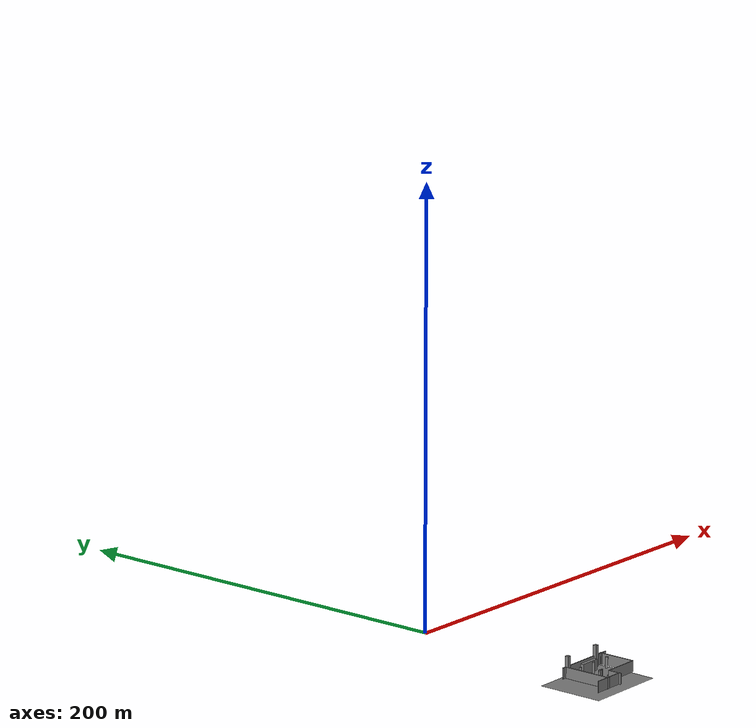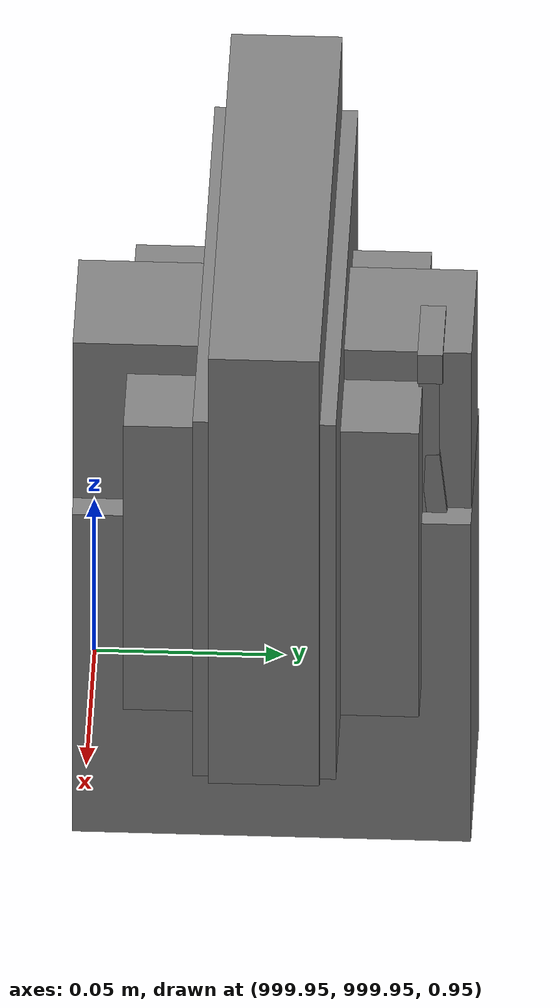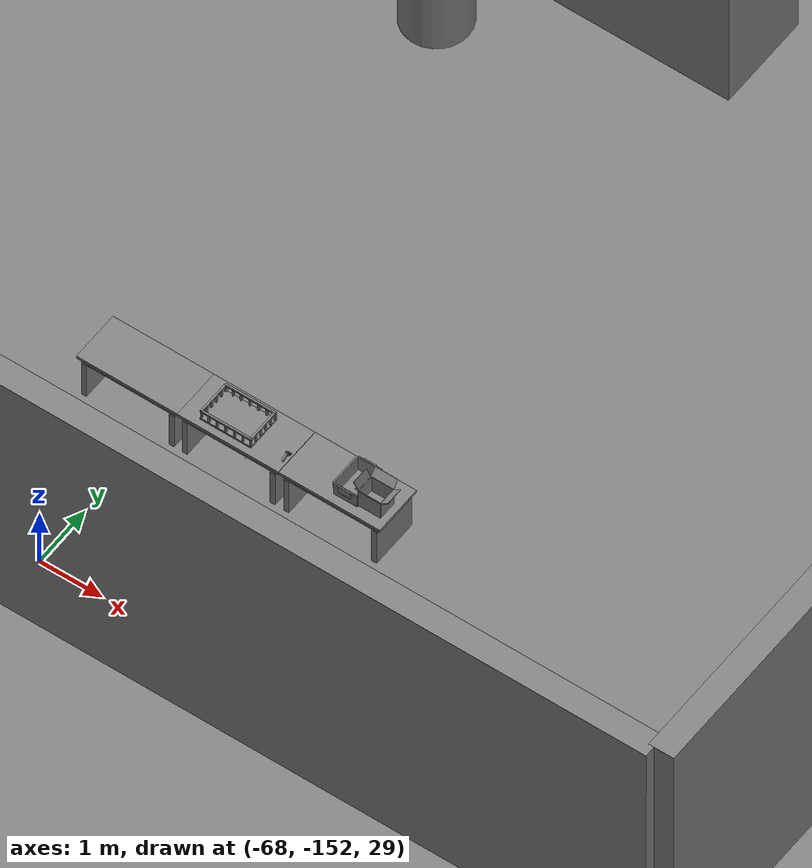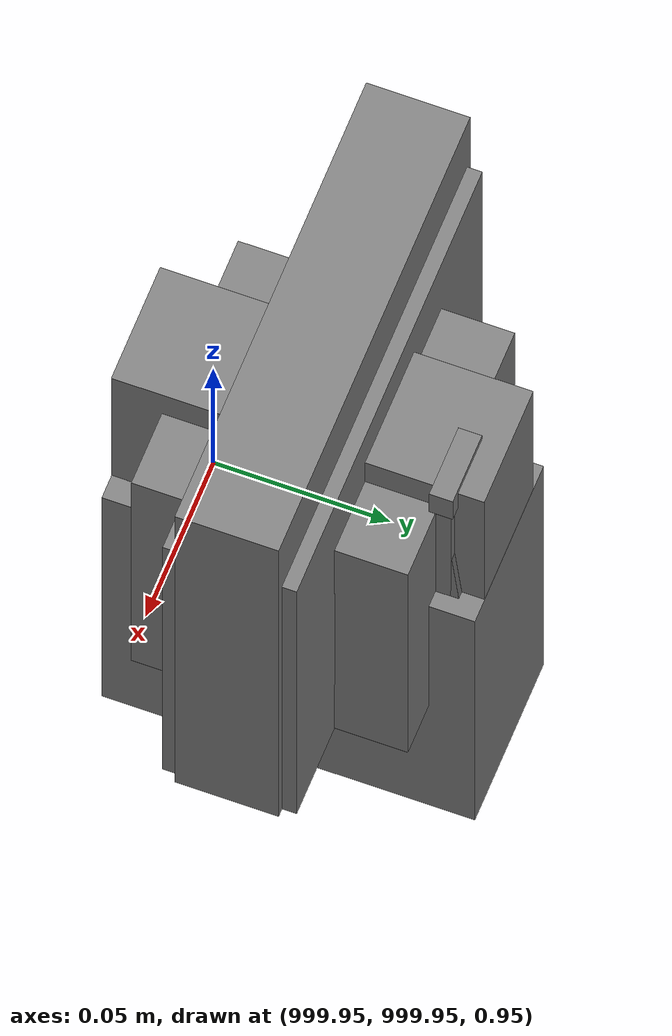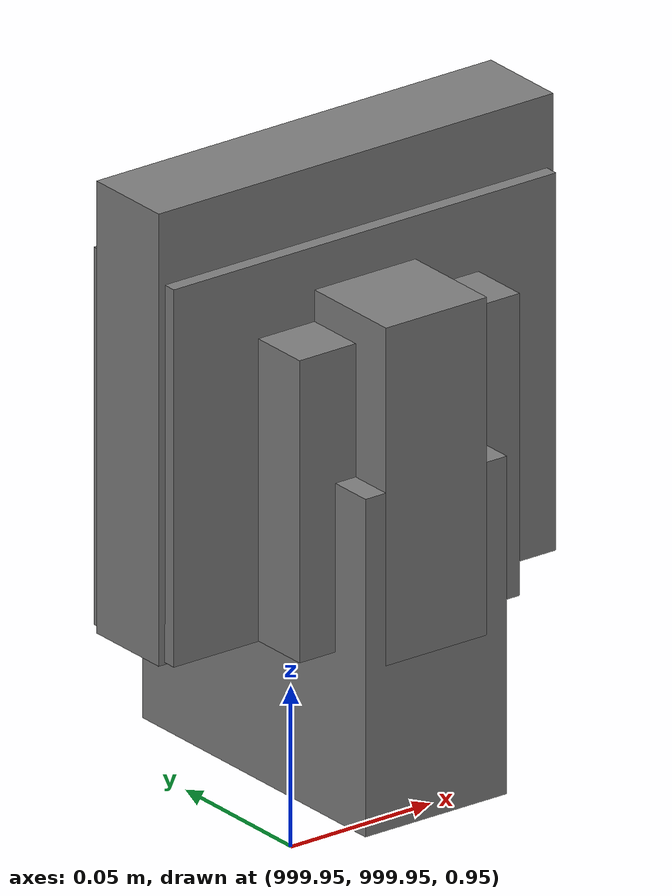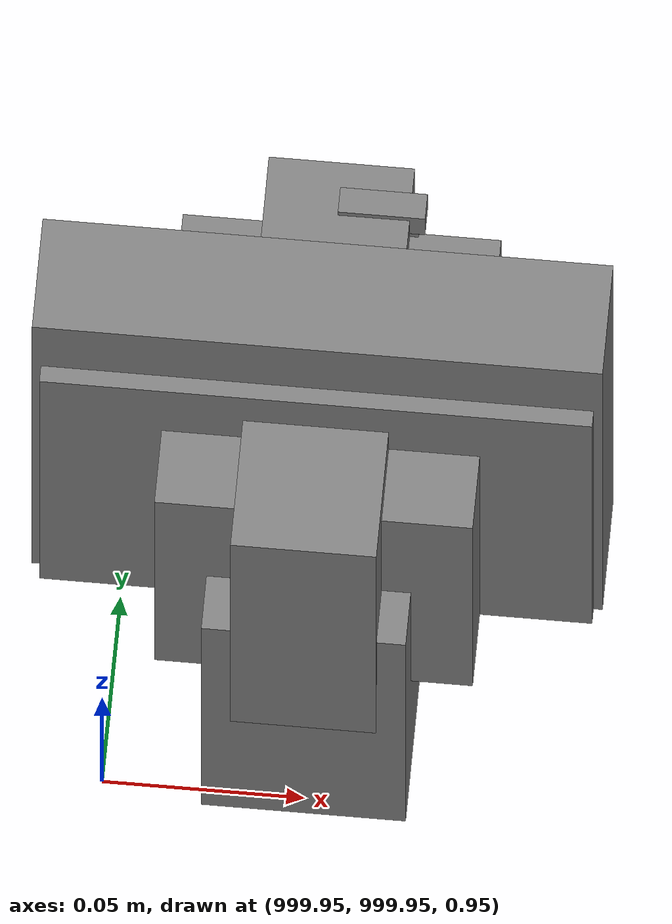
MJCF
<mujoco>
    <option gravity="0.000000000 0.000000000 -9.810000420" timestep="0.0049999999" integrator="implicitfast" density="1.225" viscosity="1.8000001e-05" noslip_iterations="10" iterations="100" sdf_iterations="50">
        <flag multiccd="disable"/>
    </option>
    <size memory="1000M"/>
    <compiler coordinate="local"/>
    <worldbody>
        <light cutoff="30" pos="0 1 1" dir="0 -1 -2"/>
        <light cutoff="30" pos="0 -1 1" dir="0 1 -2"/>
        <body pos="1000.000000000 1000.000000000 1.000000000" euler="0.000000000 0.000000000 180.000000000" name="openloong_gripper_2f85_fix_base_usda_wifi_box">
            <geom contype="1" conaffinity="1" density="1000" type="box" material="" rgba="0.500000000 0.500000000 0.500000000 1.000000000" solimp="0.899999976 0.949999988 0.001000000" friction="1.000000000 0.005000000 0.000100000" solref="0.020000000 1.000000000" margin="0" condim="3" group="0" pos="0.000000000 0.000000000 0.058978677" quat="0.000000000 0.000000047 0.000000000 1.000000000" size="0.068499997 0.018999999 0.059000000" name="openloong_gripper_2f85_fix_base_usda_geom_124D0F2A_04CF_4EDE_ADAB_11ABD07854D6"/>
            <freejoint name="openloong_gripper_2f85_fix_base_usda_wifi_box_joint"/>
            <site size="0.005000000 0.005000000 0.005000000" rgba="0.500000000 0.500000000 0.500000000 1.000000000" pos="0.000000000 0.000000000 0.000000000" quat="0.999961913 0.008726500 0.000000000 0.000000000" group="0" type="sphere" name="openloong_gripper_2f85_fix_base_usda_wifi_boxsite"/>
        </body>
        <body pos="-66.062286377 -149.329315186 31.162746429" euler="-94.186401367 12.733520508 -172.047729492" mocap="true" name="spotlight2_SpotLight"/>
        <body pos="-65.854278564 -149.213699341 31.169483185" euler="39.049919128 13.333743095 85.095779419" mocap="true" name="spotlight6_SpotLight"/>
        <body pos="1000.000000000 999.999938965 1.000000000" euler="0.000000000 0.000000000 180.000000000" name="openloong_gripper_2f85_fix_base_usda_intelcore_i5">
            <geom contype="1" conaffinity="1" density="1000" type="box" material="" rgba="0.500000000 0.500000000 0.500000000 1.000000000" solimp="0.899999976 0.949999988 0.001000000" friction="1.000000000 0.005000000 0.000100000" solref="0.020000000 1.000000000" margin="0" condim="3" group="0" pos="0.000000000 0.000000000 0.051722717" quat="0.707106709 0.000000000 0.000000000 -0.707106769" size="0.052800000 0.018080002 0.052800000" name="openloong_gripper_2f85_fix_base_usda_geom_0D744DDF_4FBD_498C_AF29_C7293F7B416B"/>
            <freejoint name="openloong_gripper_2f85_fix_base_usda_intelcore_i5_joint"/>
            <site size="0.005000000 0.005000000 0.005000000" rgba="0.500000000 0.500000000 0.500000000 1.000000000" pos="0.000000000 0.000000000 0.000000000" quat="0.999961913 0.008726534 0.000000000 0.000000000" group="0" type="sphere" name="openloong_gripper_2f85_fix_base_usda_intelcore_i5site"/>
        </body>
        <body pos="1000.000000000 1000.000000000 1.000000000" euler="0.000011953 0.000005123 -179.999984741" name="openloong_gripper_2f85_fix_base_usda_intel_box">
            <geom contype="1" conaffinity="1" density="1000" type="box" material="" rgba="0.500000000 0.500000000 0.500000000 1.000000000" solimp="0.899999976 0.949999988 0.001000000" friction="1.000000000 0.005000000 0.000100000" solref="0.020000000 1.000000000" margin="0" condim="3" group="0" pos="0.000000000 -0.000067139 0.000082284" quat="0.707106709 0.000000225 0.000000253 0.707106650" size="0.052800003 0.025300000 0.052800003" name="openloong_gripper_2f85_fix_base_usda_geom_360EF1EF_3DF6_4EFB_9159_82D543EB0881"/>
            <freejoint name="openloong_gripper_2f85_fix_base_usda_intel_box_joint"/>
            <site size="0.005000000 0.005000000 0.005000000" rgba="0.500000000 0.500000000 0.500000000 1.000000000" pos="0.000000000 0.000000000 0.000000000" quat="0.999961913 0.008726500 0.000000000 0.000000000" group="0" type="sphere" name="openloong_gripper_2f85_fix_base_usda_intel_boxsite"/>
        </body>
        <body pos="1000.000000000 1000.000000000 1.000000000" euler="0.000000000 0.000000000 180.000000000" name="openloong_gripper_2f85_fix_base_usda_cpu_fan">
            <geom contype="1" conaffinity="1" density="1000" type="box" material="" rgba="0.500000000 0.500000000 0.500000000 1.000000000" solimp="0.899999976 0.949999988 0.001000000" friction="1.000000000 0.005000000 0.000100000" solref="0.020000000 1.000000000" margin="0" condim="3" group="0" pos="0.000000000 0.000000000 0.070034981" quat="0.000000000 0.000000000 0.000000000 1.000000000" size="0.070700005 0.014699999 0.070700005" name="openloong_gripper_2f85_fix_base_usda_geom_DDA95761_F99D_4C85_85B6_CF95F5F530F8"/>
            <freejoint name="openloong_gripper_2f85_fix_base_usda_cpu_fan_joint"/>
            <site size="0.005000000 0.005000000 0.005000000" rgba="0.500000000 0.500000000 0.500000000 1.000000000" pos="0.000000000 0.000000000 0.000000000" quat="0.999961913 0.008726535 0.000000000 0.000000000" group="0" type="sphere" name="openloong_gripper_2f85_fix_base_usda_cpu_fancsite"/>
        </body>
        <body pos="1000.000000000 1000.000000000 1.000000000" euler="0.000000000 0.000000000 180.000000000" name="openloong_gripper_2f85_fix_base_usda_battery_01">
            <geom contype="1" conaffinity="1" density="1000" type="box" material="" rgba="0.500000000 0.500000000 0.500000000 1.000000000" solimp="0.899999976 0.949999988 0.001000000" friction="1.000000000 0.005000000 0.000100000" solref="0.020000000 1.000000000" margin="0" condim="3" group="0" pos="-0.011123657 -0.041940309 0.101691343" quat="1.000000000 0.000000000 0.000000000 0.000000000" size="0.010800000 0.003375000 0.004725000" name="openloong_gripper_2f85_fix_base_usda_geom_6622C43F_A32E_4C86_B232_0004057C267F"/>
            <geom contype="1" conaffinity="1" density="1000" type="box" material="" rgba="0.500000000 0.500000000 0.500000000 1.000000000" solimp="0.899999976 0.949999988 0.001000000" friction="1.000000000 0.005000000 0.000100000" solref="0.020000000 1.000000000" margin="0" condim="3" group="0" pos="-0.010876465 -0.044247437 0.047066893" quat="0.998702705 -0.050920475 0.000000000 0.000000000" size="0.009450001 0.002700000 0.024975000" name="openloong_gripper_2f85_fix_base_usda_geom_79B96410_CF61_4F3C_B5FD_547D7FE2BAA8"/>
            <geom contype="1" conaffinity="1" density="1000" type="box" material="" rgba="0.500000000 0.500000000 0.500000000 1.000000000" solimp="0.899999976 0.949999988 0.001000000" friction="1.000000000 0.005000000 0.000100000" solref="0.020000000 1.000000000" margin="0" condim="3" group="0" pos="-0.001235962 -0.000659180 0.047381196" quat="1.000000000 0.000000000 0.000000000 0.000000000" size="0.039420001 0.039150000 0.047250003" name="openloong_gripper_2f85_fix_base_usda_geom_4BC02275_CE9F_4B79_B63D_F78D4B9DB320"/>
            <geom contype="1" conaffinity="1" density="1000" type="box" material="" rgba="0.500000000 0.500000000 0.500000000 1.000000000" solimp="0.899999976 0.949999988 0.001000000" friction="1.000000000 0.005000000 0.000100000" solref="0.020000000 1.000000000" margin="0" condim="3" group="0" pos="-0.010876465 -0.039138794 0.009851727" quat="1.000000000 0.000000000 0.000000000 0.000000000" size="0.009450001 0.010800000 0.013500000" name="openloong_gripper_2f85_fix_base_usda_geom_062E4A01_1858_4A23_B707_C4FB7D0B3393"/>
            <geom contype="1" conaffinity="1" density="1000" type="box" material="" rgba="0.500000000 0.500000000 0.500000000 1.000000000" solimp="0.899999976 0.949999988 0.001000000" friction="1.000000000 0.005000000 0.000100000" solref="0.020000000 1.000000000" margin="0" condim="3" group="0" pos="-0.010876465 -0.041528322 0.071508206" quat="1.000000000 0.000000000 0.000000000 0.000000000" size="0.009450001 0.002700000 0.027000001" name="openloong_gripper_2f85_fix_base_usda_geom_914A6E5C_C7FB_460B_AD98_B48C1CFD3A49"/>
            <freejoint name="openloong_gripper_2f85_fix_base_usda_battery_01_joint"/>
            <site size="0.005000000 0.005000000 0.005000000" rgba="0.500000000 0.500000000 0.500000000 1.000000000" pos="0.000000000 0.000000000 0.000000000" quat="0.999961913 0.008726500 0.000000000 0.000000000" group="0" type="sphere" name="openloong_gripper_2f85_fix_base_usda_battery_01site"/>
        </body>
        <body pos="-66.130149841 -148.994842529 31.171474457" euler="179.800476074 52.474758148 -84.932449341" mocap="true" name="spotlight4_SpotLight"/>
        <body pos="-64.866622925 -149.383972168 30.183746338" euler="89.999984741 89.999946594 0.000000000" name="openloong_gripper_2f85_fix_base_usda_bluebox_01">
            <geom contype="1" conaffinity="1" density="1000" type="box" material="" rgba="0.500000000 0.500000000 0.500000000 1.000000000" solimp="0.899999976 0.949999988 0.001000000" friction="1.000000000 0.005000000 0.000100000" solref="0.020000000 1.000000000" margin="0" condim="3" group="0" pos="0.276580811 0.187225342 0.000068665" quat="0.707106948 0.000077471 0.707106352 0.000077486" size="0.100000001 0.057999998 0.010000000" name="openloong_gripper_2f85_fix_base_usda_geom_B14AFC95_B70D_403B_AB45_0B0F194BE876"/>
            <geom contype="1" conaffinity="1" density="1000" type="box" material="" rgba="0.500000000 0.500000000 0.500000000 1.000000000" solimp="0.899999976 0.949999988 0.001000000" friction="1.000000000 0.005000000 0.000100000" solref="0.020000000 1.000000000" margin="0" condim="3" group="0" pos="0.000000000 0.002883911 0.000000000" quat="0.999999881 0.000000000 0.000000000 0.000000000" size="0.254000008 0.003000000 0.172000006" name="openloong_gripper_2f85_fix_base_usda_geom_E7A360F0_7FF0_49F8_B8FC_875FE902F7B1"/>
            <geom contype="1" conaffinity="1" density="1000" type="box" material="" rgba="0.500000000 0.500000000 0.500000000 1.000000000" solimp="0.899999976 0.949999988 0.001000000" friction="1.000000000 0.005000000 0.000100000" solref="0.020000000 1.000000000" margin="0" condim="3" group="0" pos="0.000000000 0.124874115 0.173484802" quat="0.999796331 0.020176515 -0.000000015 0.000000030" size="0.259999990 0.119999997 0.007000000" name="openloong_gripper_2f85_fix_base_usda_geom_A6BC2AF4_E519_4E1C_961E_1D6ED2A4E519"/>
            <geom contype="1" conaffinity="1" density="1000" type="box" material="" rgba="0.500000000 0.500000000 0.500000000 1.000000000" solimp="0.899999976 0.949999988 0.001000000" friction="1.000000000 0.005000000 0.000100000" solref="0.020000000 1.000000000" margin="0" condim="3" group="0" pos="0.000000000 0.124874115 -0.173469543" quat="0.999796331 -0.020176545 -0.000000015 0.000000000" size="0.259999990 0.119999997 0.007000000" name="openloong_gripper_2f85_fix_base_usda_geom_61ED1138_7D3B_4167_A374_11C92ED01323"/>
            <geom contype="1" conaffinity="1" density="1000" type="box" material="" rgba="0.500000000 0.500000000 0.500000000 1.000000000" solimp="0.899999976 0.949999988 0.001000000" friction="1.000000000 0.005000000 0.000100000" solref="0.020000000 1.000000000" margin="0" condim="3" group="0" pos="0.000000000 0.214008331 0.188980103" quat="0.999912977 0.013176724 0.000000015 0.000000000" size="0.259999990 0.029999999 0.012500000" name="openloong_gripper_2f85_fix_base_usda_geom_8D58DBE1_5DCA_4484_A3F2_77947F7FF3D5"/>
            <geom contype="1" conaffinity="1" density="1000" type="box" material="" rgba="0.500000000 0.500000000 0.500000000 1.000000000" solimp="0.899999976 0.949999988 0.001000000" friction="1.000000000 0.005000000 0.000100000" solref="0.020000000 1.000000000" margin="0" condim="3" group="0" pos="-0.258361816 0.125289917 0.001876831" quat="0.702796936 -0.020792112 0.710783124 0.020769298" size="0.189999998 0.119999997 0.009000000" name="openloong_gripper_2f85_fix_base_usda_geom_9FEEED8E_4561_41EC_82EC_6CD81B4BF1C6"/>
            <geom contype="1" conaffinity="1" density="1000" type="box" material="" rgba="0.500000000 0.500000000 0.500000000 1.000000000" solimp="0.899999976 0.949999988 0.001000000" friction="1.000000000 0.005000000 0.000100000" solref="0.020000000 1.000000000" margin="0" condim="3" group="0" pos="0.000000000 0.214008331 -0.188980103" quat="0.999912977 -0.013176769 0.000000030 0.000000015" size="0.259999990 0.029999999 0.012500000" name="openloong_gripper_2f85_fix_base_usda_geom_FCEFAAB1_3026_4ABA_90C1_3F288DC88B43"/>
            <geom contype="1" conaffinity="1" density="1000" type="box" material="" rgba="0.500000000 0.500000000 0.500000000 1.000000000" solimp="0.899999976 0.949999988 0.001000000" friction="1.000000000 0.005000000 0.000100000" solref="0.020000000 1.000000000" margin="0" condim="3" group="0" pos="-0.276611328 0.187225342 0.000068665" quat="0.707106650 0.000077441 0.707106709 0.000077456" size="0.100000001 0.057999998 0.010000000" name="openloong_gripper_2f85_fix_base_usda_geom_C7E939C7_ABB4_4D2A_BF45_82B2C2D5F627"/>
            <geom contype="1" conaffinity="1" density="1000" type="box" material="" rgba="0.500000000 0.500000000 0.500000000 1.000000000" solimp="0.899999976 0.949999988 0.001000000" friction="1.000000000 0.005000000 0.000100000" solref="0.020000000 1.000000000" margin="0" condim="3" group="0" pos="0.258331299 0.125289917 0.001876831" quat="0.702851415 0.018856421 0.710823774 -0.019329369" size="0.189999998 0.119999997 0.009000000" name="openloong_gripper_2f85_fix_base_usda_geom_06C0D568_E3A8_41E0_BA10_9EBC0E8A6305"/>
            <freejoint name="openloong_gripper_2f85_fix_base_usda_bluebox_01_joint"/>
            <site size="0.005000000 0.005000000 0.005000000" rgba="0.500000000 0.500000000 0.500000000 1.000000000" pos="0.000000000 0.000000000 0.000000000" quat="0.999961913 0.008726534 0.000000000 0.000000000" group="0" type="sphere" name="openloong_gripper_2f85_fix_base_usda_bluebox_01site"/>
        </body>
        <body pos="-64.496299744 -149.491867065 30.235729218" euler="0.000000000 0.000000000 89.999946594" name="openloong_gripper_2f85_fix_base_usda_cardboardbox_01">
            <geom contype="1" conaffinity="1" density="1000" type="box" material="" rgba="0.500000000 0.500000000 0.500000000 1.000000000" solimp="0.899999976 0.949999988 0.001000000" friction="1.000000000 0.005000000 0.000100000" solref="0.020000000 1.000000000" margin="0" condim="3" group="0" pos="-0.003166199 -0.004086494 0.005052090" quat="1.000000000 0.000000000 0.000000000 0.000000000" size="0.142499998 0.177500010 0.005000000" name="openloong_gripper_2f85_fix_base_usda_geom_1FBC984E_8DEA_464F_8D8A_BF17AA460CAC"/>
            <geom contype="1" conaffinity="1" density="1000" type="box" material="" rgba="0.500000000 0.500000000 0.500000000 1.000000000" solimp="0.899999976 0.949999988 0.001000000" friction="1.000000000 0.005000000 0.000100000" solref="0.020000000 1.000000000" margin="0" condim="3" group="0" pos="-0.003166199 0.170316696 0.150570869" quat="1.000000000 0.000000000 0.000000000 0.000000000" size="0.142499998 0.005000000 0.149999991" name="openloong_gripper_2f85_fix_base_usda_geom_00FDF572_7E46_47F4_B95A_CAF770417E86"/>
            <geom contype="1" conaffinity="1" density="1000" type="box" material="" rgba="0.500000000 0.500000000 0.500000000 1.000000000" solimp="0.899999976 0.949999988 0.001000000" friction="1.000000000 0.005000000 0.000100000" solref="0.020000000 1.000000000" margin="0" condim="3" group="0" pos="-0.147399902 -0.005307198 0.150570869" quat="1.000000000 0.000000000 0.000000000 0.000000000" size="0.005000000 0.177500010 0.149999991" name="openloong_gripper_2f85_fix_base_usda_geom_6F4BC83B_DBDC_4C73_ACC3_2DBC8EAC2F3C"/>
            <geom contype="1" conaffinity="1" density="1000" type="box" material="" rgba="0.500000000 0.500000000 0.500000000 1.000000000" solimp="0.899999976 0.949999988 0.001000000" friction="1.000000000 0.005000000 0.000100000" solref="0.020000000 1.000000000" margin="0" condim="3" group="0" pos="0.140275955 -0.005307198 0.150570869" quat="1.000000000 0.000000000 0.000000000 0.000000000" size="0.005000000 0.177500010 0.149999991" name="openloong_gripper_2f85_fix_base_usda_geom_56E06158_2D05_4B04_A877_A41BE1F13D47"/>
            <geom contype="1" conaffinity="1" density="1000" type="box" material="" rgba="0.500000000 0.500000000 0.500000000 1.000000000" solimp="0.899999976 0.949999988 0.001000000" friction="1.000000000 0.005000000 0.000100000" solref="0.020000000 1.000000000" margin="0" condim="3" group="0" pos="-0.003166199 -0.181550980 0.150570869" quat="1.000000000 0.000000000 0.000000000 0.000000000" size="0.142499998 0.005000000 0.149999991" name="openloong_gripper_2f85_fix_base_usda_geom_AD2CC49C_FCBD_4FBC_9E43_815A28DAA146"/>
            <freejoint name="openloong_gripper_2f85_fix_base_usda_cardboardbox_01_joint"/>
            <site size="0.005000000 0.005000000 0.005000000" rgba="0.500000000 0.500000000 0.500000000 1.000000000" pos="0.000000000 0.000000000 0.000000000" quat="0.999961913 0.008726535 0.000000000 0.000000000" group="0" type="sphere" name="openloong_gripper_2f85_fix_base_usda_site_EEBFB2E9_DE90_4792_89F0_C8C997AC198F"/>
            <body pos="0.139160156 -0.004048347 0.301930904" euler="-179.999954224 49.383502960 179.999954224" name="openloong_gripper_2f85_fix_base_usda_A1_006">
                <geom contype="1" conaffinity="1" density="1000" type="box" material="" rgba="0.500000000 0.500000000 0.500000000 1.000000000" solimp="0.899999976 0.949999988 0.001000000" friction="1.000000000 0.005000000 0.000100000" solref="0.020000000 1.000000000" margin="0" condim="3" group="0" pos="-0.071587563 0.000009537 0.001745224" quat="0.999999881 0.000000000 0.000000000 0.000000000" size="0.071249999 0.179999992 0.002500000" name="openloong_gripper_2f85_fix_base_usda_geom_B7773192_9957_4314_8DF1_17E55C3F7C82"/>
                <joint armature="0" stiffness="0.07" damping="0.0099999998" axis="0.000000 1.000000 0.000000" type="hinge" name="openloong_gripper_2f85_fix_base_usda_A1_006"/>
            </body>
            <body pos="-0.145902634 -0.004086494 0.301938057" euler="-180.000000000 -60.000011444 -180.000000000" name="openloong_gripper_2f85_fix_base_usda_A2_006">
                <geom contype="1" conaffinity="1" density="1000" type="box" material="" rgba="0.500000000 0.500000000 0.500000000 1.000000000" solimp="0.899999976 0.949999988 0.001000000" friction="1.000000000 0.005000000 0.000100000" solref="0.020000000 1.000000000" margin="0" condim="3" group="0" pos="0.071268082 0.000009537 0.002717972" quat="0.000002921 0.000000000 -0.000000030 0.999999881" size="0.071249999 0.179999992 0.002500000" name="openloong_gripper_2f85_fix_base_usda_geom_CA51B55E_8C2D_485B_AD49_7933927ED5FA"/>
                <joint armature="0" stiffness="0.07" damping="0.0099999998" axis="0.000000 1.000000 0.000000" type="hinge" name="openloong_gripper_2f85_fix_base_usda_A2_006"/>
            </body>
            <body pos="-0.003385544 0.175991058 0.301930904" euler="-125.858116150 -0.000004561 0.000002331" name="openloong_gripper_2f85_fix_base_usda_B2_006">
                <geom contype="1" conaffinity="1" density="1000" type="box" material="" rgba="0.500000000 0.500000000 0.500000000 1.000000000" solimp="0.899999976 0.949999988 0.001000000" friction="1.000000000 0.005000000 0.000100000" solref="0.020000000 1.000000000" margin="0" condim="3" group="0" pos="0.000009537 -0.070939064 -0.002470016" quat="0.999614120 0.027776197 -0.000000015 0.000000030" size="0.137500003 0.064999998 0.005000000" name="openloong_gripper_2f85_fix_base_usda_geom_46C4BE31_A91F_4AF3_BDD2_63AA48EC1A81"/>
                <joint armature="0" stiffness="0.07" damping="0.0099999998" axis="1.000000 0.000000 0.000000" type="hinge" name="openloong_gripper_2f85_fix_base_usda_B2_006"/>
            </body>
            <body pos="-0.003385544 -0.184140205 0.301938057" euler="147.805557251 0.000000000 0.000000000" name="openloong_gripper_2f85_fix_base_usda_B1_006">
                <geom contype="1" conaffinity="1" density="1000" type="box" material="" rgba="0.500000000 0.500000000 0.500000000 1.000000000" solimp="0.899999976 0.949999988 0.001000000" friction="1.000000000 0.005000000 0.000100000" solref="0.020000000 1.000000000" margin="0" condim="3" group="0" pos="-0.000028610 0.070202351 -0.002703667" quat="0.999614179 -0.027776167 0.000000000 0.000000000" size="0.137500003 0.064999998 0.005000000" name="openloong_gripper_2f85_fix_base_usda_geom_93B95ED7_025B_45CA_9A9C_1785C19E5E4E"/>
                <joint armature="0" stiffness="0.07" damping="0.0099999998" axis="1.000000 0.000000 0.000000" type="hinge" name="openloong_gripper_2f85_fix_base_usda_B1_006"/>
            </body>
        </body>
        <body pos="-65.882858276 -149.481979370 30.229999542" euler="-64.487716675 0.000000000 0.000000000" name="openloong_gripper_2f85_fix_base_usda_Barcode">
            <geom contype="1" conaffinity="1" density="1000" type="box" material="" rgba="0.500000000 0.500000000 0.500000000 1.000000000" solimp="0.899999976 0.949999988 0.001000000" friction="1.000000000 0.005000000 0.000100000" solref="0.020000000 1.000000000" margin="0" condim="3" group="0" pos="0.000000000 0.013038635 0.001419067" quat="0.000000000 0.000000000 0.000000000 1.000000119" size="0.034000002 0.010000000 0.017999999" name="openloong_gripper_2f85_fix_base_usda_geom_F198928A_DFF6_4802_8387_517BEC9EA678"/>
            <geom contype="1" conaffinity="1" density="1000" type="box" material="" rgba="0.500000000 0.500000000 0.500000000 1.000000000" solimp="0.899999976 0.949999988 0.001000000" friction="1.000000000 0.005000000 0.000100000" solref="0.020000000 1.000000000" margin="0" condim="3" group="0" pos="0.000000000 -0.035301208 -0.007095337" quat="0.000000000 0.000000000 -0.043619365 0.999048233" size="0.028999999 0.010000000 0.020000000" name="openloong_gripper_2f85_fix_base_usda_geom_39922D0F_D714_4A26_AE41_CB50A85336EF"/>
            <geom contype="1" conaffinity="1" density="1000" type="box" material="" rgba="0.500000000 0.500000000 0.500000000 1.000000000" solimp="0.899999976 0.949999988 0.001000000" friction="1.000000000 0.005000000 0.000100000" solref="0.020000000 1.000000000" margin="0" condim="3" group="0" pos="0.000000000 -0.043411255 -0.011749268" quat="0.922262907 0.386563420 0.000000000 0.000000000" size="0.026000001 0.010000000 0.020000000" name="openloong_gripper_2f85_fix_base_usda_geom_ADA8C415_E36B_4163_B362_FA57D315EB1D"/>
            <geom contype="1" conaffinity="1" density="1000" type="box" material="" rgba="0.500000000 0.500000000 0.500000000 1.000000000" solimp="0.899999976 0.949999988 0.001000000" friction="1.000000000 0.005000000 0.000100000" solref="0.020000000 1.000000000" margin="0" condim="3" group="0" pos="0.000000000 -0.016967773 -0.031860352" quat="0.000000000 0.000000000 0.000000000 1.000000119" size="0.008000000 0.010000000 0.013000000" name="openloong_gripper_2f85_fix_base_usda_geom_CE15188F_81DB_4FF7_B7A9_C950462CE144"/>
            <geom contype="1" conaffinity="1" density="1000" type="box" material="" rgba="0.500000000 0.500000000 0.500000000 1.000000000" solimp="0.899999976 0.949999988 0.001000000" friction="1.000000000 0.005000000 0.000100000" solref="0.020000000 1.000000000" margin="0" condim="3" group="0" pos="0.000000000 -0.001869202 0.000312805" quat="0.953716993 0.300705761 0.000000000 0.000000000" size="0.032000002 0.010000000 0.018999999" name="openloong_gripper_2f85_fix_base_usda_geom_BC45480A_0B15_4C71_9F6F_8F1927D19EEE"/>
            <geom contype="1" conaffinity="1" density="1000" type="box" material="" rgba="0.500000000 0.500000000 0.500000000 1.000000000" solimp="0.899999976 0.949999988 0.001000000" friction="1.000000000 0.005000000 0.000100000" solref="0.020000000 1.000000000" margin="0" condim="3" group="0" pos="0.000000000 -0.019531250 -0.003173828" quat="0.953716993 0.300705761 0.000000000 0.000000000" size="0.030999999 0.010000000 0.020000000" name="openloong_gripper_2f85_fix_base_usda_geom_6BE1DF7B_9B7E_4D4A_882B_6ECFAB686558"/>
            <geom contype="1" conaffinity="1" density="1000" type="box" material="" rgba="0.500000000 0.500000000 0.500000000 1.000000000" solimp="0.899999976 0.949999988 0.001000000" friction="1.000000000 0.005000000 0.000100000" solref="0.020000000 1.000000000" margin="0" condim="3" group="0" pos="0.000000000 -0.035301208 -0.007095337" quat="0.953716993 0.300705761 0.000000000 0.000000000" size="0.028999999 0.010000000 0.020000000" name="openloong_gripper_2f85_fix_base_usda_geom_783139D0_A797_4AA8_941D_23D9EC4F16C9"/>
            <geom contype="1" conaffinity="1" density="1000" type="box" material="" rgba="0.500000000 0.500000000 0.500000000 1.000000000" solimp="0.899999976 0.949999988 0.001000000" friction="1.000000000 0.005000000 0.000100000" solref="0.020000000 1.000000000" margin="0" condim="3" group="0" pos="0.000000000 -0.042617798 -0.071121216" quat="0.000000000 0.000000000 0.000000000 1.000000119" size="0.013000000 0.021000000 0.059999999" name="openloong_gripper_2f85_fix_base_usda_geom_F8FE0816_D2CC_4C9B_9003_F11A90FF9D36"/>
            <freejoint name="openloong_gripper_2f85_fix_base_usda_Barcode_joint"/>
            <site size="0.005000000 0.005000000 0.005000000" rgba="0.500000000 0.500000000 0.500000000 1.000000000" pos="0.000000000 0.000000000 0.000000000" quat="1.000000000 0.000000000 0.000000000 0.000000000" group="0" type="sphere" name="openloong_gripper_2f85_fix_base_usda_Barcode_site"/>
        </body>
        <body pos="-66.745018005 -149.392349243 30.184000015" euler="0.000000000 0.000000000 89.999946594" name="[22331389049762]_Basket_01">
            <geom contype="1" conaffinity="1" density="1000" type="box" material="" rgba="0.500000000 0.500000000 0.500000000 1.000000000" solimp="0.899999976 0.949999988 0.001000000" friction="1.000000000 0.005000000 0.000100000" solref="0.020000000 1.000000000" margin="0" condim="3" group="0" pos="-0.052425385 0.389207840 0.089787483" quat="0.707107008 0.000000000 0.000000000 0.707106411" size="0.014249999 0.014249999 0.059999999" name="[22331389049762]_geom_D40D1758_577A_45D7_AE25_0F632BB818CE"/>
            <geom contype="1" conaffinity="1" density="1000" type="box" material="" rgba="0.500000000 0.500000000 0.500000000 1.000000000" solimp="0.899999976 0.949999988 0.001000000" friction="1.000000000 0.005000000 0.000100000" solref="0.020000000 1.000000000" margin="0" condim="3" group="0" pos="0.264015198 -0.133043289 0.089787483" quat="0.707107008 0.000000000 0.000000000 0.707106411" size="0.014249999 0.014249999 0.059999999" name="[22331389049762]_geom_8F419AA2_4B20_41E1_8772_D92DA8791668"/>
            <geom contype="1" conaffinity="1" density="1000" type="box" material="" rgba="0.500000000 0.500000000 0.500000000 1.000000000" solimp="0.899999976 0.949999988 0.001000000" friction="1.000000000 0.005000000 0.000100000" solref="0.020000000 1.000000000" margin="0" condim="3" group="0" pos="-0.264015198 -0.265548706 0.089793205" quat="0.707107008 0.000000000 0.000000000 0.707106411" size="0.014249999 0.014249999 0.059999999" name="[22331389049762]_geom_52FD2C60_DF0E_43F8_A4EA_C4481ADEE90A"/>
            <geom contype="1" conaffinity="1" density="1000" type="box" material="" rgba="0.500000000 0.500000000 0.500000000 1.000000000" solimp="0.899999976 0.949999988 0.001000000" friction="1.000000000 0.005000000 0.000100000" solref="0.020000000 1.000000000" margin="0" condim="3" group="0" pos="-0.160263062 -0.389322281 0.089793205" quat="0.707107008 0.000000000 0.000000000 0.707106411" size="0.014249999 0.014249999 0.059999999" name="[22331389049762]_geom_9B29D3DE_3A02_4692_B36F_7789B94D7241"/>
            <geom contype="1" conaffinity="1" density="1000" type="box" material="" rgba="0.500000000 0.500000000 0.500000000 1.000000000" solimp="0.899999976 0.949999988 0.001000000" friction="1.000000000 0.005000000 0.000100000" solref="0.020000000 1.000000000" margin="0" condim="3" group="0" pos="0.162265778 -0.389322281 0.089787483" quat="0.707107008 0.000000000 0.000000000 0.707106411" size="0.014249999 0.014249999 0.059999999" name="[22331389049762]_geom_03D3BC03_B6B3_485C_AB5F_5BC0F5479F64"/>
            <geom contype="1" conaffinity="1" density="1000" type="box" material="" rgba="0.500000000 0.500000000 0.500000000 1.000000000" solimp="0.899999976 0.949999988 0.001000000" friction="1.000000000 0.005000000 0.000100000" solref="0.020000000 1.000000000" margin="0" condim="3" group="0" pos="0.264015198 0.389207840 0.089787483" quat="0.707107008 0.000000000 0.000000000 0.707106411" size="0.014249999 0.014249999 0.059999999" name="[22331389049762]_geom_574E6157_3CFC_4C58_B590_8309CC617D89"/>
            <geom contype="1" conaffinity="1" density="1000" type="box" material="" rgba="0.500000000 0.500000000 0.500000000 1.000000000" solimp="0.899999976 0.949999988 0.001000000" friction="1.000000000 0.005000000 0.000100000" solref="0.020000000 1.000000000" margin="0" condim="3" group="0" pos="-0.264015198 -0.133043289 0.089793205" quat="0.707107008 0.000000000 0.000000000 0.707106411" size="0.014249999 0.014249999 0.059999999" name="[22331389049762]_geom_4AC2653C_33DA_4651_9974_753290F799E8"/>
            <geom contype="1" conaffinity="1" density="1000" type="box" material="" rgba="0.500000000 0.500000000 0.500000000 1.000000000" solimp="0.899999976 0.949999988 0.001000000" friction="1.000000000 0.005000000 0.000100000" solref="0.020000000 1.000000000" margin="0" condim="3" group="0" pos="-0.264026642 0.269256592 0.089793205" quat="0.707107008 0.000000000 0.000000000 0.707106411" size="0.014249999 0.014249999 0.059999999" name="[22331389049762]_geom_91647F18_A017_41B9_99C5_3BF2F1E767B3"/>
            <geom contype="1" conaffinity="1" density="1000" type="box" material="" rgba="0.500000000 0.500000000 0.500000000 1.000000000" solimp="0.899999976 0.949999988 0.001000000" friction="1.000000000 0.005000000 0.000100000" solref="0.020000000 1.000000000" margin="0" condim="3" group="0" pos="0.054462433 0.389207840 0.089787483" quat="0.707107008 0.000000000 0.000000000 0.707106411" size="0.014249999 0.014249999 0.059999999" name="[22331389049762]_geom_E144A98F_D383_4589_BD91_CB1CA8A708ED"/>
            <geom contype="1" conaffinity="1" density="1000" type="box" material="" rgba="0.500000000 0.500000000 0.500000000 1.000000000" solimp="0.899999976 0.949999988 0.001000000" friction="1.000000000 0.005000000 0.000100000" solref="0.020000000 1.000000000" margin="0" condim="3" group="0" pos="0.054462433 -0.389322281 0.089787483" quat="0.707107008 0.000000000 0.000000000 0.707106411" size="0.014249999 0.014249999 0.059999999" name="[22331389049762]_geom_BDE2424F_8866_411D_A2F9_E40E7F8BC7AA"/>
            <geom contype="1" conaffinity="1" density="1000" type="box" material="" rgba="0.500000000 0.500000000 0.500000000 1.000000000" solimp="0.899999976 0.949999988 0.001000000" friction="1.000000000 0.005000000 0.000100000" solref="0.020000000 1.000000000" margin="0" condim="3" group="0" pos="0.264015198 0.269256592 0.089793205" quat="0.707107008 0.000000000 0.000000000 0.707106411" size="0.014249999 0.014249999 0.059999999" name="[22331389049762]_geom_7AC941BF_463B_436F_9282_EDE0FDA4E8BA"/>
            <geom contype="1" conaffinity="1" density="1000" type="box" material="" rgba="0.500000000 0.500000000 0.500000000 1.000000000" solimp="0.899999976 0.949999988 0.001000000" friction="1.000000000 0.005000000 0.000100000" solref="0.020000000 1.000000000" margin="0" condim="3" group="0" pos="0.264015198 -0.389322281 0.089787483" quat="0.707107008 0.000000000 0.000000000 0.707106411" size="0.014249999 0.014249999 0.059999999" name="[22331389049762]_geom_86C98800_5619_4AFB_809C_BCC889008E0D"/>
            <geom contype="1" conaffinity="1" density="1000" type="box" material="" rgba="0.500000000 0.500000000 0.500000000 1.000000000" solimp="0.899999976 0.949999988 0.001000000" friction="1.000000000 0.005000000 0.000100000" solref="0.020000000 1.000000000" margin="0" condim="3" group="0" pos="0.000000000 0.000000000 0.015998840" quat="0.707107008 0.000000000 0.000000000 0.707106411" size="0.403499991 0.279000014 0.015750000" name="[22331389049762]_geom_535C2CC1_3C5A_4F54_8F1C_4B3FEF2F3720"/>
            <geom contype="1" conaffinity="1" density="1000" type="box" material="" rgba="0.500000000 0.500000000 0.500000000 1.000000000" solimp="0.899999976 0.949999988 0.001000000" friction="1.000000000 0.005000000 0.000100000" solref="0.020000000 1.000000000" margin="0" condim="3" group="0" pos="0.000000000 -0.389476776 0.163619041" quat="0.707107008 0.000000000 0.000000000 0.707106411" size="0.015000000 0.277500004 0.015750000" name="[22331389049762]_geom_861FF396_DDBB_4648_B80A_7C112EBADA44"/>
            <geom contype="1" conaffinity="1" density="1000" type="box" material="" rgba="0.500000000 0.500000000 0.500000000 1.000000000" solimp="0.899999976 0.949999988 0.001000000" friction="1.000000000 0.005000000 0.000100000" solref="0.020000000 1.000000000" margin="0" condim="3" group="0" pos="0.162265778 0.389207840 0.089787483" quat="0.707107008 0.000000000 0.000000000 0.707106411" size="0.014249999 0.014249999 0.059999999" name="[22331389049762]_geom_9859B990_A4A2_4DAC_AA2C_1FCA4E35C394"/>
            <geom contype="1" conaffinity="1" density="1000" type="box" material="" rgba="0.500000000 0.500000000 0.500000000 1.000000000" solimp="0.899999976 0.949999988 0.001000000" friction="1.000000000 0.005000000 0.000100000" solref="0.020000000 1.000000000" margin="0" condim="3" group="0" pos="0.000000000 0.389471054 0.163619041" quat="0.707107008 0.000000000 0.000000000 0.707106411" size="0.015000000 0.277500004 0.015750000" name="[22331389049762]_geom_7091FF62_91DF_4B91_8E15_388946AB6A09"/>
            <geom contype="1" conaffinity="1" density="1000" type="box" material="" rgba="0.500000000 0.500000000 0.500000000 1.000000000" solimp="0.899999976 0.949999988 0.001000000" friction="1.000000000 0.005000000 0.000100000" solref="0.020000000 1.000000000" margin="0" condim="3" group="0" pos="-0.263511658 0.000000000 0.163619041" quat="0.707107008 0.000000000 0.000000000 0.707106411" size="0.403499991 0.015000000 0.015750000" name="[22331389049762]_geom_359C9F59_0B9A_42E0_AFB9_4A4FA9695FFB"/>
            <geom contype="1" conaffinity="1" density="1000" type="box" material="" rgba="0.500000000 0.500000000 0.500000000 1.000000000" solimp="0.899999976 0.949999988 0.001000000" friction="1.000000000 0.005000000 0.000100000" solref="0.020000000 1.000000000" margin="0" condim="3" group="0" pos="-0.264015198 0.141334534 0.089793205" quat="0.707107008 0.000000000 0.000000000 0.707106411" size="0.014249999 0.014249999 0.059999999" name="[22331389049762]_geom_54C8BF33_F168_472A_96D9_5FFDF97805FA"/>
            <geom contype="1" conaffinity="1" density="1000" type="box" material="" rgba="0.500000000 0.500000000 0.500000000 1.000000000" solimp="0.899999976 0.949999988 0.001000000" friction="1.000000000 0.005000000 0.000100000" solref="0.020000000 1.000000000" margin="0" condim="3" group="0" pos="0.264015198 -0.265548706 0.089787483" quat="0.707107008 0.000000000 0.000000000 0.707106411" size="0.014249999 0.014249999 0.059999999" name="[22331389049762]_geom_8514770D_B214_429A_A54F_3C2C2300255A"/>
            <geom contype="1" conaffinity="1" density="1000" type="box" material="" rgba="0.500000000 0.500000000 0.500000000 1.000000000" solimp="0.899999976 0.949999988 0.001000000" friction="1.000000000 0.005000000 0.000100000" solref="0.020000000 1.000000000" margin="0" condim="3" group="0" pos="-0.160263062 0.389207840 0.089787483" quat="0.707107008 0.000000000 0.000000000 0.707106411" size="0.014249999 0.014249999 0.059999999" name="[22331389049762]_geom_4DD3B62F_FC73_46C0_BB10_391601FFC871"/>
            <geom contype="1" conaffinity="1" density="1000" type="box" material="" rgba="0.500000000 0.500000000 0.500000000 1.000000000" solimp="0.899999976 0.949999988 0.001000000" friction="1.000000000 0.005000000 0.000100000" solref="0.020000000 1.000000000" margin="0" condim="3" group="0" pos="-0.052425385 -0.389322281 0.089787483" quat="0.707107008 0.000000000 0.000000000 0.707106411" size="0.014249999 0.014249999 0.059999999" name="[22331389049762]_geom_B7879171_782B_4653_B42D_B30721D752C2"/>
            <geom contype="1" conaffinity="1" density="1000" type="box" material="" rgba="0.500000000 0.500000000 0.500000000 1.000000000" solimp="0.899999976 0.949999988 0.001000000" friction="1.000000000 0.005000000 0.000100000" solref="0.020000000 1.000000000" margin="0" condim="3" group="0" pos="-0.264026642 -0.389322281 0.089793205" quat="0.707107008 0.000000000 0.000000000 0.707106411" size="0.014249999 0.014249999 0.059999999" name="[22331389049762]_geom_009ABCE1_910F_4654_ACBF_0D098E03D91F"/>
            <geom contype="1" conaffinity="1" density="1000" type="box" material="" rgba="0.500000000 0.500000000 0.500000000 1.000000000" solimp="0.899999976 0.949999988 0.001000000" friction="1.000000000 0.005000000 0.000100000" solref="0.020000000 1.000000000" margin="0" condim="3" group="0" pos="0.264015198 0.141334534 0.089787483" quat="0.707107008 0.000000000 0.000000000 0.707106411" size="0.014249999 0.014249999 0.059999999" name="[22331389049762]_geom_CFCBBE5F_48D0_4CCA_960B_9C4CA3CFAFE4"/>
            <geom contype="1" conaffinity="1" density="1000" type="box" material="" rgba="0.500000000 0.500000000 0.500000000 1.000000000" solimp="0.899999976 0.949999988 0.001000000" friction="1.000000000 0.005000000 0.000100000" solref="0.020000000 1.000000000" margin="0" condim="3" group="0" pos="-0.264015198 0.389207840 0.089793205" quat="0.707107008 0.000000000 0.000000000 0.707106411" size="0.014249999 0.014249999 0.059999999" name="[22331389049762]_geom_39255FAF_4915_40AC_9B3E_F28408ECE598"/>
            <geom contype="1" conaffinity="1" density="1000" type="box" material="" rgba="0.500000000 0.500000000 0.500000000 1.000000000" solimp="0.899999976 0.949999988 0.001000000" friction="1.000000000 0.005000000 0.000100000" solref="0.020000000 1.000000000" margin="0" condim="3" group="0" pos="0.264015198 0.004480362 0.089787483" quat="0.707107008 0.000000000 0.000000000 0.707106411" size="0.014249999 0.014249999 0.059999999" name="[22331389049762]_geom_AAC411EC_ED7D_49EC_9D29_A0D179ECBB60"/>
            <geom contype="1" conaffinity="1" density="1000" type="box" material="" rgba="0.500000000 0.500000000 0.500000000 1.000000000" solimp="0.899999976 0.949999988 0.001000000" friction="1.000000000 0.005000000 0.000100000" solref="0.020000000 1.000000000" margin="0" condim="3" group="0" pos="0.263694763 -0.000011444 0.163619041" quat="0.707107008 0.000000000 0.000000000 0.707106411" size="0.403499991 0.015000000 0.015750000" name="[22331389049762]_geom_4D794E80_BB2E_4897_B436_A460D0B3D667"/>
            <geom contype="1" conaffinity="1" density="1000" type="box" material="" rgba="0.500000000 0.500000000 0.500000000 1.000000000" solimp="0.899999976 0.949999988 0.001000000" friction="1.000000000 0.005000000 0.000100000" solref="0.020000000 1.000000000" margin="0" condim="3" group="0" pos="-0.264015198 0.004480362 0.089793205" quat="0.707107008 0.000000000 0.000000000 0.707106411" size="0.014249999 0.014249999 0.059999999" name="[22331389049762]_geom_F2DA9EE7_D680_4D2A_A412_F9B33DCB2196"/>
            <freejoint name="[22331389049762]_joint_D1918FAC_9E43_4E7B_9BBC_F6847C37603A"/>
        </body>
        <body pos="0.000000000 0.000000000 0.000000000" euler="0.000000000 0.000000000 0.000000000" name="Static Objects_Static Objects">
            <geom contype="1" conaffinity="1" density="1000" type="box" material="" rgba="0.500000000 0.500000000 0.500000000 1.000000000" solimp="0.899999976 0.949999988 0.001000000" friction="1.000000000 0.005000000 0.000100000" solref="0.020000000 1.000000000" margin="0" condim="3" group="0" pos="-67.544113159 -149.365814209 29.727830887" quat="0.500000417 0.499999970 0.499999553 0.499999970" size="0.381000012 0.319999993 0.041000001" name="Static Objects_geom_A23DACCD_F36D_420D_803E_486808DB0177"/>
            <geom contype="1" conaffinity="1" density="1000" type="box" material="" rgba="0.500000000 0.500000000 0.500000000 1.000000000" solimp="0.899999976 0.949999988 0.001000000" friction="1.000000000 0.005000000 0.000100000" solref="0.020000000 1.000000000" margin="0" condim="3" group="0" pos="-68.239501953 -149.365814209 30.086868286" quat="0.500000417 0.499999970 0.499999553 0.499999970" size="0.370999992 0.039500002 0.745000005" name="Static Objects_geom_7575CAB8_16B6_4E4E_A410_1A47ADD60CCE"/>
            <geom contype="1" conaffinity="1" density="1000" type="box" material="" rgba="0.500000000 0.500000000 0.500000000 1.000000000" solimp="0.899999976 0.949999988 0.001000000" friction="1.000000000 0.005000000 0.000100000" solref="0.020000000 1.000000000" margin="0" condim="3" group="0" pos="-68.239501953 -149.365814209 30.147235870" quat="0.500000417 0.499999970 0.499999553 0.499999970" size="0.400000006 0.022000000 0.800000012" name="Static Objects_geom_788923D4_CC59_4EB3_8266_ECAF7E1C4269"/>
            <geom contype="1" conaffinity="1" density="1000" type="box" material="" rgba="0.500000000 0.500000000 0.500000000 1.000000000" solimp="0.899999976 0.949999988 0.001000000" friction="1.000000000 0.005000000 0.000100000" solref="0.020000000 1.000000000" margin="0" condim="3" group="0" pos="-68.934890747 -149.365814209 29.727830887" quat="0.500000417 0.499999970 0.499999553 0.499999970" size="0.381000012 0.319999993 0.041000001" name="Static Objects_geom_AE063246_2858_4E5E_8961_438CD5B124DF"/>
            <geom contype="1" conaffinity="1" density="1000" type="box" material="" rgba="0.500000000 0.500000000 0.500000000 1.000000000" solimp="0.899999976 0.949999988 0.001000000" friction="1.000000000 0.005000000 0.000100000" solref="0.020000000 1.000000000" margin="0" condim="3" group="0" pos="-68.239501953 -149.365814209 29.561563492" quat="0.500000417 0.499999970 0.499999553 0.499999970" size="0.020000000 0.022000000 0.660000026" name="Static Objects_geom_A76F4DFC_83CD_40C6_AAEE_F0F932CC545D"/>
            <geom contype="1" conaffinity="1" density="1000" type="box" material="" rgba="0.500000000 0.500000000 0.500000000 1.000000000" solimp="0.899999976 0.949999988 0.001000000" friction="1.000000000 0.005000000 0.000100000" solref="0.020000000 1.000000000" margin="0" condim="3" group="0" pos="-65.945671082 -149.365814209 29.727830887" quat="0.500000417 0.499999970 0.499999553 0.499999970" size="0.381000012 0.319999993 0.041000001" name="Static Objects_geom_9D380D49_A902_49DE_B6BF_395A719A42CC"/>
            <geom contype="1" conaffinity="1" density="1000" type="box" material="" rgba="0.500000000 0.500000000 0.500000000 1.000000000" solimp="0.899999976 0.949999988 0.001000000" friction="1.000000000 0.005000000 0.000100000" solref="0.020000000 1.000000000" margin="0" condim="3" group="0" pos="-66.641059875 -149.365814209 30.086868286" quat="0.500000417 0.499999970 0.499999553 0.499999970" size="0.370999992 0.039500002 0.745000005" name="Static Objects_geom_76B8B7D5_5AA4_4C67_BEB5_8C58760B2098"/>
            <geom contype="1" conaffinity="1" density="1000" type="box" material="" rgba="0.500000000 0.500000000 0.500000000 1.000000000" solimp="0.899999976 0.949999988 0.001000000" friction="1.000000000 0.005000000 0.000100000" solref="0.020000000 1.000000000" margin="0" condim="3" group="0" pos="-66.641059875 -149.365814209 30.147235870" quat="0.500000417 0.499999970 0.499999553 0.499999970" size="0.400000006 0.022000000 0.800000012" name="Static Objects_geom_96577DBE_EB5E_4FAA_9359_4C9C64A607BA"/>
            <geom contype="1" conaffinity="1" density="1000" type="box" material="" rgba="0.500000000 0.500000000 0.500000000 1.000000000" solimp="0.899999976 0.949999988 0.001000000" friction="1.000000000 0.005000000 0.000100000" solref="0.020000000 1.000000000" margin="0" condim="3" group="0" pos="-67.336448669 -149.365814209 29.727830887" quat="0.500000417 0.499999970 0.499999553 0.499999970" size="0.381000012 0.319999993 0.041000001" name="Static Objects_geom_23556A35_8070_4402_A9EE_93A754069672"/>
            <geom contype="1" conaffinity="1" density="1000" type="box" material="" rgba="0.500000000 0.500000000 0.500000000 1.000000000" solimp="0.899999976 0.949999988 0.001000000" friction="1.000000000 0.005000000 0.000100000" solref="0.020000000 1.000000000" margin="0" condim="3" group="0" pos="-66.641059875 -149.365814209 29.561563492" quat="0.500000417 0.499999970 0.499999553 0.499999970" size="0.020000000 0.022000000 0.660000026" name="Static Objects_geom_0E560DB2_846C_4D31_AFC3_153C96E021F5"/>
            <geom contype="1" conaffinity="1" density="1000" type="box" material="" rgba="0.500000000 0.500000000 0.500000000 1.000000000" solimp="0.899999976 0.949999988 0.001000000" friction="1.000000000 0.005000000 0.000100000" solref="0.020000000 1.000000000" margin="0" condim="3" group="0" pos="-64.338577271 -149.365814209 29.727830887" quat="0.500000417 0.499999970 0.499999553 0.499999970" size="0.381000012 0.319999993 0.041000001" name="Static Objects_geom_BEC00AA9_64A9_4276_A29E_DD9B59B09ECF"/>
            <geom contype="1" conaffinity="1" density="1000" type="box" material="" rgba="0.500000000 0.500000000 0.500000000 1.000000000" solimp="0.899999976 0.949999988 0.001000000" friction="1.000000000 0.005000000 0.000100000" solref="0.020000000 1.000000000" margin="0" condim="3" group="0" pos="-65.033966064 -149.365814209 30.086868286" quat="0.500000417 0.499999970 0.499999553 0.499999970" size="0.370999992 0.039500002 0.745000005" name="Static Objects_geom_96B70D1B_D799_4C07_99E9_301BD789FEEC"/>
            <geom contype="1" conaffinity="1" density="1000" type="box" material="" rgba="0.500000000 0.500000000 0.500000000 1.000000000" solimp="0.899999976 0.949999988 0.001000000" friction="1.000000000 0.005000000 0.000100000" solref="0.020000000 1.000000000" margin="0" condim="3" group="0" pos="-65.033966064 -149.365814209 30.147235870" quat="0.500000417 0.499999970 0.499999553 0.499999970" size="0.400000006 0.022000000 0.800000012" name="Static Objects_geom_98AB324B_C005_4B3B_98BE_2A225F092102"/>
            <geom contype="1" conaffinity="1" density="1000" type="box" material="" rgba="0.500000000 0.500000000 0.500000000 1.000000000" solimp="0.899999976 0.949999988 0.001000000" friction="1.000000000 0.005000000 0.000100000" solref="0.020000000 1.000000000" margin="0" condim="3" group="0" pos="-65.729354858 -149.365814209 29.727830887" quat="0.500000417 0.499999970 0.499999553 0.499999970" size="0.381000012 0.319999993 0.041000001" name="Static Objects_geom_DDF5E04D_C029_4AAE_9E70_F2B72A028CCA"/>
            <geom contype="1" conaffinity="1" density="1000" type="box" material="" rgba="0.500000000 0.500000000 0.500000000 1.000000000" solimp="0.899999976 0.949999988 0.001000000" friction="1.000000000 0.005000000 0.000100000" solref="0.020000000 1.000000000" margin="0" condim="3" group="0" pos="-65.033966064 -149.365814209 29.561563492" quat="0.500000417 0.499999970 0.499999553 0.499999970" size="0.020000000 0.022000000 0.660000026" name="Static Objects_geom_50CF2979_CB2B_4C56_87B9_9C0631F075BF"/>
            <geom contype="1" conaffinity="1" density="1000" type="box" material="" rgba="0.500000000 0.500000000 0.500000000 1.000000000" solimp="0.899999976 0.949999988 0.001000000" friction="1.000000000 0.005000000 0.000100000" solref="0.020000000 1.000000000" margin="0" condim="3" group="0" pos="-61.754566193 -137.853729248 33.906845093" quat="0.707107067 0.000000000 0.000000000 0.707106471" size="0.759999990 0.759999990 4.500000000" name="Static Objects_geom_CFBCCE70_B273_4256_89CE_209292867132"/>
            <geom contype="1" conaffinity="1" density="1000" type="box" material="" rgba="0.500000000 0.500000000 0.500000000 1.000000000" solimp="0.899999976 0.949999988 0.001000000" friction="1.000000000 0.005000000 0.000100000" solref="0.020000000 1.000000000" margin="0" condim="3" group="0" pos="-57.511135101 -144.927108765 31.707921982" quat="1.000000000 0.000000000 0.000000000 0.000000000" size="0.200000003 8.000000000 2.299999952" name="Static Objects_geom_4B7AD673_548D_490D_AB9B_B74B005D65E2"/>
            <geom contype="1" conaffinity="1" density="1000" type="box" material="" rgba="0.500000000 0.500000000 0.500000000 1.000000000" solimp="0.899999976 0.949999988 0.001000000" friction="1.000000000 0.005000000 0.000100000" solref="0.020000000 1.000000000" margin="0" condim="3" group="0" pos="-80.517646790 -157.574050903 31.688196182" quat="0.707107067 0.000000000 0.000000000 0.707106471" size="0.600000024 0.600000024 2.299999952" name="Static Objects_geom_160E45EE_C66F_41F7_AFD8_ADE2BB4FCB53"/>
            <geom contype="1" conaffinity="1" density="1000" type="box" material="" rgba="0.500000000 0.500000000 0.500000000 1.000000000" solimp="0.899999976 0.949999988 0.001000000" friction="1.000000000 0.005000000 0.000100000" solref="0.020000000 1.000000000" margin="0" condim="3" group="0" pos="-80.711044312 -147.414932251 31.666158676" quat="1.000000000 0.000000000 0.000000000 0.000000000" size="0.200000003 10.000000000 2.299999952" name="Static Objects_geom_51A1775D_0102_4EFE_A68D_0F0A6B8B29D3"/>
            <geom contype="1" conaffinity="1" density="1000" type="box" material="" rgba="0.500000000 0.500000000 0.500000000 1.000000000" solimp="0.899999976 0.949999988 0.001000000" friction="1.000000000 0.005000000 0.000100000" solref="0.020000000 1.000000000" margin="0" condim="3" group="0" pos="-57.687217712 -137.434692383 31.688196182" quat="0.707107067 0.000000000 0.000000000 0.707106471" size="0.600000024 0.600000024 2.299999952" name="Static Objects_geom_9FC274D9_958B_4AE7_84E9_DE62F3079BC0"/>
            <geom contype="1" conaffinity="1" density="1000" type="box" material="" rgba="0.500000000 0.500000000 0.500000000 1.000000000" solimp="0.899999976 0.949999988 0.001000000" friction="1.000000000 0.005000000 0.000100000" solref="0.020000000 1.000000000" margin="0" condim="3" group="0" pos="-69.537033081 -140.263229370 31.714921951" quat="0.707107067 0.000000000 0.000000000 0.707106471" size="0.759999990 4.500000000 2.299999952" name="Static Objects_geom_46748CE1_3A19_480C_909D_645FAE8BB4F2"/>
            <geom contype="1" conaffinity="1" density="1000" type="box" material="" rgba="0.500000000 0.500000000 0.500000000 1.000000000" solimp="0.899999976 0.949999988 0.001000000" friction="1.000000000 0.005000000 0.000100000" solref="0.020000000 1.000000000" margin="0" condim="3" group="0" pos="-80.073638916 -137.853713989 33.906845093" quat="0.707107067 0.000000000 0.000000000 0.707106471" size="0.759999990 0.759999990 4.500000000" name="Static Objects_geom_35D4CF30_ECAF_4A67_A26D_AA5956965C8B"/>
            <geom contype="1" conaffinity="1" density="1000" type="box" material="" rgba="0.500000000 0.500000000 0.500000000 1.000000000" solimp="0.899999976 0.949999988 0.001000000" friction="1.000000000 0.005000000 0.000100000" solref="0.020000000 1.000000000" margin="0" condim="3" group="0" pos="-73.406707764 -155.734664917 31.707921982" quat="1.000000000 0.000000000 0.000000000 0.000000000" size="0.200000003 3.000000000 2.299999952" name="Static Objects_geom_796A7C5F_8D32_4823_B310_AD917C83317E"/>
            <geom contype="1" conaffinity="1" density="1000" type="box" material="" rgba="0.500000000 0.500000000 0.500000000 1.000000000" solimp="0.899999976 0.949999988 0.001000000" friction="1.000000000 0.005000000 0.000100000" solref="0.020000000 1.000000000" margin="0" condim="3" group="0" pos="-68.497543335 -137.448257446 31.707921982" quat="0.707107067 0.000000000 0.000000000 0.707106471" size="0.200000003 14.000000000 2.299999952" name="Static Objects_geom_894478A1_9E82_482B_8A8B_E18F0D0533F3"/>
            <geom contype="1" conaffinity="1" density="1000" type="cylinder" material="" rgba="0.500000000 0.500000000 0.500000000 1.000000000" solimp="0.899999976 0.949999988 0.001000000" friction="1.000000000 0.005000000 0.000100000" solref="0.020000000 1.000000000" margin="0" condim="3" group="0" pos="-68.868522644 -142.134506226 31.711090088" quat="0.707107067 0.000000000 0.000000000 0.707106471" size="0.509999990 2.299999952 1.000000000" name="Static Objects_geom_80F53328_1AF3_417C_B757_65B73AB997EF"/>
            <geom contype="1" conaffinity="1" density="1000" type="plane" material="" rgba="0.500000000 0.500000000 0.500000000 1.000000000" solimp="0.899999976 0.949999988 0.001000000" friction="1.000000000 0.005000000 0.000100000" solref="0.020000000 1.000000000" margin="0" condim="3" group="0" pos="-72.873703003 -147.131927490 29.409669876" quat="1.000000000 0.000000000 0.000000000 0.000000000" size="18.000000000 14.000000000 1.000000000" name="Static Objects_geom_F93CD2CF_1857_47BC_BF6F_044BD07C354B"/>
            <geom contype="1" conaffinity="1" density="1000" type="box" material="" rgba="0.500000000 0.500000000 0.500000000 1.000000000" solimp="0.899999976 0.949999988 0.001000000" friction="1.000000000 0.005000000 0.000100000" solref="0.020000000 1.000000000" margin="0" condim="3" group="0" pos="-79.943580627 -157.782272339 31.707921982" quat="0.707107067 0.000000000 0.000000000 0.707106471" size="0.200000003 7.000000000 2.299999952" name="Static Objects_geom_5FD37C36_0693_40F9_83B3_257DDC7D8275"/>
            <geom contype="1" conaffinity="1" density="1000" type="box" material="" rgba="0.500000000 0.500000000 0.500000000 1.000000000" solimp="0.899999976 0.949999988 0.001000000" friction="1.000000000 0.005000000 0.000100000" solref="0.020000000 1.000000000" margin="0" condim="3" group="0" pos="-65.421028137 -152.903442383 31.707921982" quat="0.707107067 0.000000000 0.000000000 0.707106471" size="0.200000003 7.800000191 2.299999952" name="Static Objects_geom_18920402_81FC_4300_ACC6_EE371DE7894D"/>
            <geom contype="1" conaffinity="1" density="1000" type="box" material="" rgba="0.500000000 0.500000000 0.500000000 1.000000000" solimp="0.899999976 0.949999988 0.001000000" friction="1.000000000 0.005000000 0.000100000" solref="0.020000000 1.000000000" margin="0" condim="3" group="0" pos="-74.776908875 -149.964416504 31.688196182" quat="1.000000000 0.000000000 0.000000000 0.000000000" size="0.600000024 0.409999996 2.299999952" name="Static Objects_geom_34931887_5266_4564_8831_9AF66BAD6862"/>
            <geom contype="1" conaffinity="1" density="1000" type="cylinder" material="" rgba="0.500000000 0.500000000 0.500000000 1.000000000" solimp="0.899999976 0.949999988 0.001000000" friction="1.000000000 0.005000000 0.000100000" solref="0.020000000 1.000000000" margin="0" condim="3" group="0" pos="-60.161884308 -142.134506226 31.711090088" quat="0.707107067 0.000000000 0.000000000 0.707106471" size="0.509999990 2.299999952 1.000000000" name="Static Objects_geom_E1416B81_92FD_47A8_95D4_A2108BAD2AF5"/>
            <geom contype="1" conaffinity="1" density="1000" type="cylinder" material="" rgba="0.500000000 0.500000000 0.500000000 1.000000000" solimp="0.899999976 0.949999988 0.001000000" friction="1.000000000 0.005000000 0.000100000" solref="0.020000000 1.000000000" margin="0" condim="3" group="0" pos="-75.382453918 -149.963455200 31.711090088" quat="0.707107067 0.000000000 0.000000000 0.707106471" size="0.409999996 2.299999952 1.000000000" name="Static Objects_geom_B0388923_4D4C_4260_85BD_EF8B42F8A773"/>
            <geom contype="1" conaffinity="1" density="1000" type="cylinder" material="" rgba="0.500000000 0.500000000 0.500000000 1.000000000" solimp="0.899999976 0.949999988 0.001000000" friction="1.000000000 0.005000000 0.000100000" solref="0.020000000 1.000000000" margin="0" condim="3" group="0" pos="-74.154960632 -149.963455200 31.711090088" quat="0.707107067 0.000000000 0.000000000 0.707106471" size="0.409999996 2.299999952 1.000000000" name="Static Objects_geom_8E0B56E3_71FA_4B0C_8EDB_701DFE544BEC"/>
            <geom contype="1" conaffinity="1" density="1000" type="cylinder" material="" rgba="0.500000000 0.500000000 0.500000000 1.000000000" solimp="0.899999976 0.949999988 0.001000000" friction="1.000000000 0.005000000 0.000100000" solref="0.020000000 1.000000000" margin="0" condim="3" group="0" pos="-77.566612244 -142.134506226 31.711090088" quat="0.707107067 0.000000000 0.000000000 0.707106471" size="0.509999990 2.299999952 1.000000000" name="Static Objects_geom_BC804EEF_D6C9_426D_8930_FA1C263A3F9F"/>
        </body>
        <body pos="-66.291030884 -149.869689941 29.018842697" euler="0.000000000 0.000000000 89.999946594" mocap="true" name="openloong_gripper_2f85_fix_base_usda_leftHandMocap"/>
        <body pos="-66.291030884 -149.869689941 29.018842697" euler="0.000000000 0.000000000 89.999946594" mocap="true" name="openloong_gripper_2f85_fix_base_usda_rightHandMocap"/>
        <body pos="-66.291030884 -149.869689941 30.218843460" euler="0.000000000 0.000000000 89.999946594" name="openloong_gripper_2f85_fix_base_usda_base_link">
            <geom contype="1" conaffinity="1" density="1000" type="mesh" material="" rgba="0.783999979 0.783999979 0.783999979 1.000000000" solimp="0.899999976 0.949999988 0.001000000" friction="1.000000000 0.005000000 0.000100000" solref="0.020000000 1.000000000" margin="0" condim="3" group="3" mesh="base_link" pos="0.000000000 0.000000000 0.000000000" quat="1.000000000 0.000000000 0.000000000 0.000000000" size="1.000000000 1.000000000 1.000000000" name="openloong_gripper_2f85_fix_base_usda__geom_7_E62FD910_BA57_49B5_9F61_3401DE4A0E05"/>
            <site size="0.005000000 0.005000000 0.005000000" rgba="0.500000000 0.500000000 0.500000000 1.000000000" pos="0.000000000 0.000000000 0.000000000" quat="1.000000000 0.000000000 0.000000000 0.000000000" group="0" type="sphere" name="openloong_gripper_2f85_fix_base_usda_imu"/>
            <inertial mass="22.447001" pos="-0.005664100 -0.001336700 0.238289997" diaginertia="0.374352545 0.277180195 0.220617250" quat="0.999247074 0.035235517 -0.015086859 0.006023135"/>
            <body pos="0.000000000 0.000000000 0.299997330" euler="0.000000000 0.000000000 0.000000000" name="openloong_gripper_2f85_fix_base_usda_dummy_body">
                <geom contype="1" conaffinity="1" density="1000" type="sphere" material="" rgba="0.783999979 0.783999979 0.783999979 1.000000000" solimp="0.899999976 0.949999988 0.001000000" friction="1.000000000 0.005000000 0.000100000" solref="0.020000000 1.000000000" margin="0" condim="3" group="3" pos="0.000000000 0.000000000 0.000000000" quat="1.000000000 0.000000000 0.000000000 0.000000000" size="0.010000000 0.000000000 0.000000000" name="openloong_gripper_2f85_fix_base_usda__geom_8_BBC4EE8E_7B2B_4FDD_9C5B_A92F68EC9C44"/>
                <joint armature="0.0099999998" stiffness="0" damping="0.1" axis="0.000000 0.000000 1.000000" type="hinge" name="openloong_gripper_2f85_fix_base_usda_dummy_joint"/>
                <site size="0.010000000 0.005000000 0.005000000" rgba="0.500000000 0.500000000 0.500000000 1.000000000" pos="0.000000000 0.000000000 0.000000000" quat="1.000000000 0.000000000 0.000000000 0.000000000" group="3" type="sphere" name="openloong_gripper_2f85_fix_base_usda_dummy_site"/>
            </body>
            <body pos="0.009002686 0.000000000 0.406400681" euler="0.000000000 0.000000000 0.000000000" name="openloong_gripper_2f85_fix_base_usda_Link_head_yaw">
                <geom contype="1" conaffinity="1" density="1000" type="mesh" material="" rgba="0.783999979 0.783999979 0.783999979 1.000000000" solimp="0.899999976 0.949999988 0.001000000" friction="1.000000000 0.005000000 0.000100000" solref="0.020000000 1.000000000" margin="0" condim="3" group="3" mesh="Link_head_yaw" pos="0.000000000 0.000000000 0.000000000" quat="1.000000000 0.000000000 0.000000000 0.000000000" size="1.000000000 1.000000000 1.000000000" name="openloong_gripper_2f85_fix_base_usda__geom_10_E7B23B55_05A1_47AA_9758_E195524A0CFB"/>
                <inertial mass="0.84249002" pos="0.000000000 -0.002081400 0.044801001" diaginertia="0.000700588 0.000629000 0.000553812" quat="0.706933022 -0.015675601 0.015677100 0.706933022"/>
                <body pos="0.000000000 -0.034599304 0.048500061" euler="0.000000000 0.000000000 0.000000000" name="openloong_gripper_2f85_fix_base_usda_Link_head_pitch">
                    <geom contype="1" conaffinity="1" density="1000" type="mesh" material="" rgba="0.783999979 0.783999979 0.783999979 1.000000000" solimp="0.899999976 0.949999988 0.001000000" friction="1.000000000 0.005000000 0.000100000" solref="0.020000000 1.000000000" margin="0" condim="3" group="3" mesh="Link_head_pitch" pos="0.000000000 0.000000000 0.000000000" quat="1.000000000 0.000000000 0.000000000 0.000000000" size="1.000000000 1.000000000 1.000000000" name="openloong_gripper_2f85_fix_base_usda__geom_12_CFF7AC8E_495A_4FCC_A81D_A32A6EF8AFCA"/>
                    <inertial mass="1.3943" pos="0.020569000 0.033004001 0.125000000" diaginertia="0.006381400 0.006289940 0.004481460" quat="0.973390222 0.008406822 0.228157058 0.019624906"/>
                    <body pos="0.000000000 0.029998779 0.000000000" euler="0.000000000 0.000000000 0.000000000" name="openloong_gripper_2f85_fix_base_usda_neck_center_body">
                        <site size="0.010000000 0.005000000 0.005000000" rgba="0.500000000 0.500000000 0.500000000 1.000000000" pos="0.000000000 0.000000000 0.000000000" quat="1.000000000 0.000000000 0.000000000 0.000000000" group="3" type="sphere" name="openloong_gripper_2f85_fix_base_usda_neck_center_site"/>
                        <body pos="0.020004272 0.000000000 0.149999619" euler="-0.000002229 39.998176575 -90.000205994" name="openloong_gripper_2f85_fix_base_usda_camera_head">
                            <site size="0.010000000 0.005000000 0.005000000" rgba="0.500000000 0.500000000 0.500000000 1.000000000" pos="0.000000000 0.000000000 0.000000000" quat="1.000000000 0.000000000 0.000000000 0.000000000" group="3" type="sphere" name="openloong_gripper_2f85_fix_base_usda_camera_head_site"/>
                        </body>
                    </body>
                </body>
            </body>
            <body pos="0.003997803 -0.161598206 0.392200470" euler="0.000000000 0.000000000 0.000000000" name="openloong_gripper_2f85_fix_base_usda_Link_arm_r_01">
                <geom contype="1" conaffinity="1" density="1000" type="mesh" material="" rgba="0.783999979 0.783999979 0.783999979 1.000000000" solimp="0.899999976 0.949999988 0.001000000" friction="1.000000000 0.005000000 0.000100000" solref="0.020000000 1.000000000" margin="0" condim="3" group="3" mesh="Link_arm_r_01" pos="0.000000000 0.000000000 0.000000000" quat="1.000000000 0.000000000 0.000000000 0.000000000" size="1.000000000 1.000000000 1.000000000" name="openloong_gripper_2f85_fix_base_usda__geom_14_CB471B34_6219_4F4A_9AD0_1BA9EAF765B3"/>
                <joint armature="0.0099999998" stiffness="0" damping="1" axis="0.000000 -1.000000 0.000000" limited="true" range="-170.000015259 170.000015259" type="hinge" name="openloong_gripper_2f85_fix_base_usda_J_arm_r_01"/>
                <inertial mass="0.75641" pos="0.004494600 -0.038293999 -0.000001874" diaginertia="0.000842990 0.000803050 0.000587120" quat="-0.000163502 0.707098067 0.000812463 0.707115054"/>
                <body pos="-0.041992188 -0.041000366 0.000000000" euler="0.000000000 0.000000000 0.000000000" name="openloong_gripper_2f85_fix_base_usda_Link_arm_r_02">
                    <geom contype="1" conaffinity="1" density="1000" type="mesh" material="" rgba="0.783999979 0.783999979 0.783999979 1.000000000" solimp="0.899999976 0.949999988 0.001000000" friction="1.000000000 0.005000000 0.000100000" solref="0.020000000 1.000000000" margin="0" condim="3" group="3" mesh="Link_arm_r_02" pos="0.000000000 0.000000000 0.000000000" quat="1.000000000 0.000000000 0.000000000 0.000000000" size="1.000000000 1.000000000 1.000000000" name="openloong_gripper_2f85_fix_base_usda__geom_16_07FDF0EB_62CA_4F34_9B9B_39C62BB51C36"/>
                    <joint armature="0.0099999998" stiffness="0" damping="1" axis="-1.000000 0.000000 0.000000" limited="true" range="-105.000244141 105.000244141" type="hinge" name="openloong_gripper_2f85_fix_base_usda_J_arm_r_02"/>
                    <inertial mass="0.98500001" pos="0.041999999 -0.067430697 0.000000000" diaginertia="0.002262690 0.001730990 0.001154020" quat="0.500000000 0.500000000 -0.500000000 0.500000000"/>
                    <body pos="0.041992188 -0.122596741 0.000000000" euler="0.000000000 0.000000000 0.000000000" name="openloong_gripper_2f85_fix_base_usda_Link_arm_r_03">
                        <geom contype="1" conaffinity="1" density="1000" type="mesh" material="" rgba="0.783999979 0.783999979 0.783999979 1.000000000" solimp="0.899999976 0.949999988 0.001000000" friction="1.000000000 0.005000000 0.000100000" solref="0.020000000 1.000000000" margin="0" condim="3" group="3" mesh="Link_arm_r_03" pos="0.000000000 0.000000000 0.000000000" quat="1.000000000 0.000000000 0.000000000 0.000000000" size="1.000000000 1.000000000 1.000000000" name="openloong_gripper_2f85_fix_base_usda__geom_18_C23775D3_9349_4DFC_BDB3_68FD98786403"/>
                        <joint armature="0.0099999998" stiffness="0" damping="1" axis="0.000000 -1.000000 0.000000" limited="true" range="-170.000015259 170.000015259" type="hinge" name="openloong_gripper_2f85_fix_base_usda_J_arm_r_03"/>
                        <inertial mass="0.95899999" pos="-0.001413580 -0.164663002 0.020757901" diaginertia="0.002101340 0.002064590 0.000754802" quat="0.560480952 0.454391927 -0.443732947 0.531497955"/>
                        <body pos="0.035293579 -0.177406311 0.023998260" euler="0.000000000 0.000000000 0.000000000" name="openloong_gripper_2f85_fix_base_usda_Link_arm_r_04">
                            <geom contype="1" conaffinity="1" density="1000" type="mesh" material="" rgba="0.783999979 0.783999979 0.783999979 1.000000000" solimp="0.899999976 0.949999988 0.001000000" friction="1.000000000 0.005000000 0.000100000" solref="0.020000000 1.000000000" margin="0" condim="3" group="3" mesh="Link_arm_r_04" pos="0.000000000 0.000000000 0.000000000" quat="1.000000000 0.000000000 0.000000000 0.000000000" size="1.000000000 1.000000000 1.000000000" name="openloong_gripper_2f85_fix_base_usda__geom_20_F0CC7B39_537F_4AC2_BDFE_62893FE1E432"/>
                            <joint armature="0.0099999998" stiffness="0" damping="1" axis="-1.000000 0.000000 0.000000" limited="true" range="0.000000000 170.000015259" type="hinge" name="openloong_gripper_2f85_fix_base_usda_J_arm_r_04"/>
                            <inertial mass="0.60000002" pos="-0.038727000 -0.060766999 -0.021003000" diaginertia="0.001092610 0.000712422 0.000645102" quat="0.327701002 0.632602990 -0.467366993 0.523443997"/>
                            <body pos="-0.035293579 -0.103492737 -0.023998260" euler="0.000000000 0.000000000 0.000000000" name="openloong_gripper_2f85_fix_base_usda_Link_arm_r_05">
                                <geom contype="1" conaffinity="1" density="1000" type="mesh" material="" rgba="0.783999979 0.783999979 0.783999979 1.000000000" solimp="0.899999976 0.949999988 0.001000000" friction="1.000000000 0.005000000 0.000100000" solref="0.020000000 1.000000000" margin="0" condim="3" group="3" mesh="Link_arm_r_05" pos="0.000000000 0.000000000 0.000000000" quat="1.000000000 0.000000000 0.000000000 0.000000000" size="1.000000000 1.000000000 1.000000000" name="openloong_gripper_2f85_fix_base_usda__geom_22_92E4C6F3_4701_40B8_8F0F_47CE6AF8570B"/>
                                <joint armature="0.0099999998" stiffness="0" damping="1" axis="0.000000 -1.000000 0.000000" limited="true" range="-170.000015259 170.000015259" type="hinge" name="openloong_gripper_2f85_fix_base_usda_J_arm_r_05"/>
                                <inertial mass="0.68976003" pos="0.000032712 -0.068658002 -0.000111780" diaginertia="0.002522510 0.002411100 0.000448695" quat="0.707660973 0.706543028 -0.002603360 0.002470550"/>
                                <body pos="-0.026489258 -0.196502686 0.000000000" euler="0.000000000 0.000000000 0.000000000" name="openloong_gripper_2f85_fix_base_usda_Link_arm_r_06">
                                    <geom contype="1" conaffinity="1" density="1000" type="mesh" material="" rgba="0.783999979 0.783999979 0.783999979 1.000000000" solimp="0.899999976 0.949999988 0.001000000" friction="1.000000000 0.005000000 0.000100000" solref="0.020000000 1.000000000" margin="0" condim="3" group="3" mesh="Link_arm_r_06" pos="0.000000000 0.000000000 0.000000000" quat="1.000000000 0.000000000 0.000000000 0.000000000" size="1.000000000 1.000000000 1.000000000" name="openloong_gripper_2f85_fix_base_usda__geom_24_4AE75135_2E4D_4417_BECB_7649B1025305"/>
                                    <joint armature="0.0099999998" stiffness="0" damping="1" axis="1.000000 0.000000 0.000000" limited="true" range="-105.000244141 105.000244141" type="hinge" name="openloong_gripper_2f85_fix_base_usda_J_arm_r_06"/>
                                    <inertial mass="0.28" pos="0.026078001 -0.000000896 0.001663700" diaginertia="0.000156930 0.000145601 0.000104979" quat="0.707080841 0.001851080 0.001883810 0.707127810"/>
                                    <body pos="0.026489258 0.000000000 0.031799316" euler="0.000000000 0.000000000 0.000000000" name="openloong_gripper_2f85_fix_base_usda_Link_arm_r_07">
                                        <geom contype="1" conaffinity="1" density="1000" type="mesh" material="" rgba="0.783999979 0.783999979 0.783999979 1.000000000" solimp="0.899999976 0.949999988 0.001000000" friction="1.000000000 0.005000000 0.000100000" solref="0.020000000 1.000000000" margin="0" condim="3" group="3" mesh="Link_arm_r_07" pos="0.000000000 0.000000000 0.000000000" quat="1.000000000 0.000000000 0.000000000 0.000000000" size="1.000000000 1.000000000 1.000000000" name="openloong_gripper_2f85_fix_base_usda__geom_26_88987BD8_09D6_4475_85F5_653188ED68CF"/>
                                        <joint armature="0.0099999998" stiffness="0" damping="1" axis="0.000000 0.000000 1.000000" limited="true" range="-60.000133514 60.000133514" type="hinge" name="openloong_gripper_2f85_fix_base_usda_J_arm_r_07"/>
                                        <inertial mass="0.61353999" pos="-0.007859000 -0.158170000 -0.027736001" diaginertia="0.003037610 0.002570910 0.000729379" quat="0.427542925 0.443532884 -0.553093910 0.560867906"/>
                                        <body pos="0.000000000 0.286994934 -0.270000458" euler="150.000350952 -0.000001649 -0.000000442" name="openloong_gripper_2f85_fix_base_usda_camera_wrist_r">
                                            <site size="0.010000000 0.005000000 0.005000000" rgba="0.500000000 0.500000000 0.500000000 1.000000000" pos="0.000000000 0.000000000 0.000000000" quat="1.000000000 0.000000000 0.000000000 0.000000000" group="3" type="sphere" name="openloong_gripper_2f85_fix_base_usda_camera_wrist_r_site"/>
                                        </body>
                                        <body pos="0.000000000 -0.220008850 -0.033002853" euler="0.000000000 0.000000000 179.999969482" name="openloong_gripper_2f85_fix_base_usda_ee_center_body_r">
                                            <site size="0.010000000 0.005000000 0.005000000" rgba="0.500000000 0.500000000 0.500000000 1.000000000" pos="0.000000000 0.000000000 0.000000000" quat="1.000000000 0.000000000 0.000000000 0.000000000" group="3" type="sphere" name="openloong_gripper_2f85_fix_base_usda_ee_center_site_r"/>
                                        </body>
                                        <body pos="0.000000000 -0.066001892 -0.031000137" euler="89.999984741 0.000000000 180.000000000" name="openloong_gripper_2f85_fix_base_usda_zbr_base_link">
                                            <geom contype="1" conaffinity="1" density="1000" type="mesh" material="" rgba="0.783999979 0.783999979 0.783999979 1.000000000" solimp="0.899999976 0.949999988 0.001000000" friction="1.000000000 0.005000000 0.000100000" solref="0.020000000 1.000000000" margin="0" condim="3" group="3" mesh="base" pos="0.000000000 0.000003815 -0.000007629" quat="1.000000000 0.000000000 0.000000000 0.000000000" size="1.000000238 1.000000238 1.000000238" name="openloong_gripper_2f85_fix_base_usda__geom_30_6AAD2211_B59D_4577_A120_72885DC6D26D"/>
                                            <inertial mass="0.77744102" pos="0.000000000 -0.000027039 0.035467502" diaginertia="0.000260285 0.000225381 0.000152708" quat="0.999998808 -0.001528488 0.000000000 0.000000000"/>
                                            <body pos="-0.030609138 0.004745484 0.065696731" euler="-89.999984741 -0.000000000 0.000000000" name="openloong_gripper_2f85_fix_base_usda_r_left_driver">
                                                <geom contype="1" conaffinity="1" density="1000" type="mesh" material="" rgba="0.783999979 0.783999979 0.783999979 1.000000000" solimp="0.899999976 0.949999988 0.001000000" friction="1.000000000 0.005000000 0.000100000" solref="0.020000000 1.000000000" margin="0" condim="3" group="3" mesh="driver" pos="0.030609138 0.054901138 -0.004699708" quat="0.707106829 0.707106709 0.000000000 -0.000000000" size="1.000000238 1.000000238 1.000000238" name="openloong_gripper_2f85_fix_base_usda__geom_32_8978E259_01B6_4F3F_9FEE_BC324A21ED06"/>
                                                <joint armature="0.0049999999" stiffness="0" damping="0.1" axis="0.000000 0.000000 1.000000" limited="true" range="0.000000000 51.566200256" type="hinge" name="openloong_gripper_2f85_fix_base_usda_r_left_driver_joint"/>
                                                <inertial mass="0.0089956298" pos="0.000000000 0.017754700 0.001073140" diaginertia="0.000001724 0.000001609 0.000000322" quat="0.681301236 0.732003212 0.000000000 0.000000000"/>
                                                <body pos="-0.031402595 0.004524232 -0.010200503" euler="0.000000000 0.000000000 180.000000000" name="openloong_gripper_2f85_fix_base_usda_r_left_coupler">
                                                    <geom contype="1" conaffinity="1" density="1000" type="mesh" material="" rgba="0.783999979 0.783999979 0.783999979 1.000000000" solimp="0.899999976 0.949999988 0.001000000" friction="1.000000000 0.005000000 0.000100000" solref="0.020000000 1.000000000" margin="0" condim="3" group="3" mesh="coupler" pos="-0.062011734 -0.050354015 0.005500795" quat="0.707106829 -0.707106709 0.000000000 -0.000000000" size="1.000000238 1.000000238 1.000000238" name="openloong_gripper_2f85_fix_base_usda__geom_34_2C493F62_BB45_40FC_8290_769B05332A94"/>
                                                    <inertial mass="0.0140974" pos="0.000000000 0.003012090 0.023217499" diaginertia="0.000004162 0.000003522 0.000000888" quat="0.705635548 -0.045590367 0.045590367 0.705635548"/>
                                                </body>
                                            </body>
                                            <body pos="-0.012695315 -0.012001040 0.072212234" euler="-89.999984741 -0.000000000 0.000000000" name="openloong_gripper_2f85_fix_base_usda_r_left_spring_link">
                                                <geom contype="1" conaffinity="1" density="1000" type="mesh" material="" rgba="0.783999979 0.783999979 0.783999979 1.000000000" solimp="0.899999976 0.949999988 0.001000000" friction="1.000000000 0.005000000 0.000100000" solref="0.020000000 1.000000000" margin="0" condim="3" group="3" mesh="spring_link" pos="0.012695315 0.061416641 0.012050631" quat="0.707106829 0.707106709 0.000000000 -0.000000000" size="1.000000238 1.000000238 1.000000238" name="openloong_gripper_2f85_fix_base_usda__geom_36_BDA5DC24_31CD_4EAC_8CC6_97D8BA768F3F"/>
                                                <joint armature="0.001" stiffness="0.050000001" damping="0.00125" axis="0.000000 0.000000 1.000000" limited="true" range="-17.000000000 51.566200256" type="hinge" name="openloong_gripper_2f85_fix_base_usda_r_left_spring_link_joint"/>
                                                <inertial mass="0.0221642" pos="-0.000000009 0.018162400 0.021265799" diaginertia="0.000008969 0.000006717 0.000002639" quat="0.663403213 -0.244737089 0.244737089 0.663403213"/>
                                                <body pos="-0.038208015 -0.042503368 0.002950669" euler="180.000000000 0.000000000 -0.002185660" name="openloong_gripper_2f85_fix_base_usda_r_left_follower">
                                                    <geom contype="1" conaffinity="1" density="1000" type="mesh" material="" rgba="0.783999979 0.783999979 0.783999979 1.000000000" solimp="0.899999976 0.949999988 0.001000000" friction="1.000000000 0.005000000 0.000100000" solref="0.020000000 1.000000000" margin="0" condim="3" group="3" mesh="tongue" pos="0.050918590 -0.103920005 -0.009099962" quat="0.707106829 -0.707106709 0.000000030 0.000000030" size="1.000000238 1.000000238 1.000000238" name="openloong_gripper_2f85_fix_base_usda__geom_40_82B459D1_5762_48B5_9DAB_720496EB752E"/>
                                                    <geom contype="1" conaffinity="1" density="1000" type="mesh" material="" rgba="0.783999979 0.783999979 0.783999979 1.000000000" solimp="0.899999976 0.949999988 0.001000000" friction="1.000000000 0.005000000 0.000100000" solref="0.020000000 1.000000000" margin="0" condim="3" group="3" mesh="follower" pos="0.050918590 -0.103920005 -0.009099962" quat="0.707106829 -0.707106709 0.000000030 0.000000030" size="1.000000238 1.000000238 1.000000238" name="openloong_gripper_2f85_fix_base_usda__geom_39_A82EDEDB_45F0_4B24_BE94_781CDC481880"/>
                                                    <joint armature="0.001" stiffness="0" damping="0.1" axis="0.000000 0.000000 1.000000" limited="true" range="-49.999961853 51.566200256" type="hinge" name="openloong_gripper_2f85_fix_base_usda_r_left_follower"/>
                                                    <inertial mass="0.0125222" pos="0.000000000 -0.011046000 0.012478600" diaginertia="0.000002674 0.000002456 0.000000602" quat="0.986436546 0.164143041 0.000000000 0.000000000"/>
                                                    <body pos="-0.037765510 -0.103912376 -0.009099962" euler="-89.999984741 0.000000000 0.000004829" name="openloong_gripper_2f85_fix_base_usda_r_left_pad">
                                                        <geom contype="1" conaffinity="1" density="1000" type="box" material="" rgba="0.550000012 0.550000012 0.550000012 1.000000000" solimp="0.949999988 0.990000010 0.001000000" friction="0.699999988 0.005000000 0.000100000" solref="0.020000000 1.000000000" margin="0" condim="3" group="3" mass="1e-06" pos="0.043243419 0.000003815 0.119995147" quat="0.999999881 0.000000000 0.000000000 0.000000000" size="0.002000001 0.011000003 0.009375002" name="openloong_gripper_2f85_fix_base_usda_r_left_pad1_B50C729E_393B_43D9_8987_9CF9E430A9DA"/>
                                                        <geom contype="1" conaffinity="1" density="1000" type="box" material="" rgba="0.449999988 0.449999988 0.449999988 1.000000000" solimp="0.949999988 0.990000010 0.001000000" friction="0.600000024 0.005000000 0.000100000" solref="0.020000000 1.000000000" margin="0" condim="3" group="3" mass="1e-06" pos="0.043243419 0.000003815 0.138748199" quat="0.999999881 0.000000000 0.000000000 0.000000000" size="0.002000001 0.011000003 0.009375002" name="openloong_gripper_2f85_fix_base_usda_r_left_pad2_71F1F9CE_5E77_451F_ADE6_093176846080"/>
                                                    </body>
                                                </body>
                                            </body>
                                            <body pos="0.030593880 -0.004753114 0.065696731" euler="89.999984741 0.000000000 180.000000000" name="openloong_gripper_2f85_fix_base_usda_r_right_driver">
                                                <geom contype="1" conaffinity="1" density="1000" type="mesh" material="" rgba="0.783999979 0.783999979 0.783999979 1.000000000" solimp="0.899999976 0.949999988 0.001000000" friction="1.000000000 0.005000000 0.000100000" solref="0.020000000 1.000000000" margin="0" condim="3" group="3" mesh="driver" pos="0.030593880 0.054901138 -0.004699708" quat="0.707106829 0.707106709 0.000000000 0.000000000" size="1.000000238 1.000000238 1.000000238" name="openloong_gripper_2f85_fix_base_usda__geom_42_70F08754_B532_4CAA_ACC7_DF6092ECC9C1"/>
                                                <joint armature="0.0049999999" stiffness="0" damping="0.1" axis="0.000000 0.000000 1.000000" limited="true" range="0.000000000 51.566200256" type="hinge" name="openloong_gripper_2f85_fix_base_usda_r_right_driver_joint"/>
                                                <inertial mass="0.0089956298" pos="0.000000000 0.017754700 0.001073140" diaginertia="0.000001724 0.000001609 0.000000322" quat="0.681301236 0.732003212 0.000000000 0.000000000"/>
                                                <body pos="-0.031417854 0.004531861 -0.010202411" euler="0.000000000 0.000000000 180.000000000" name="openloong_gripper_2f85_fix_base_usda_r_right_coupler">
                                                    <geom contype="1" conaffinity="1" density="1000" type="mesh" material="" rgba="0.783999979 0.783999979 0.783999979 1.000000000" solimp="0.899999976 0.949999988 0.001000000" friction="1.000000000 0.005000000 0.000100000" solref="0.020000000 1.000000000" margin="0" condim="3" group="3" mesh="coupler" pos="-0.062042251 -0.050376903 0.005500795" quat="0.707106829 -0.707106709 0.000000000 0.000000000" size="1.000000238 1.000000238 1.000000238" name="openloong_gripper_2f85_fix_base_usda__geom_44_962EE6F9_C458_45C6_A93A_B5F2481A5669"/>
                                                    <inertial mass="0.0140974" pos="0.000000000 0.003012090 0.023217499" diaginertia="0.000004162 0.000003522 0.000000888" quat="0.705635548 -0.045590367 0.045590367 0.705635548"/>
                                                </body>
                                            </body>
                                            <body pos="0.012695315 0.011997226 0.072219864" euler="89.999984741 0.000000000 180.000000000" name="openloong_gripper_2f85_fix_base_usda_r_right_spring_link">
                                                <geom contype="1" conaffinity="1" density="1000" type="mesh" material="" rgba="0.783999979 0.783999979 0.783999979 1.000000000" solimp="0.899999976 0.949999988 0.001000000" friction="1.000000000 0.005000000 0.000100000" solref="0.020000000 1.000000000" margin="0" condim="3" group="3" mesh="spring_link" pos="0.012695315 0.061424270 0.012048724" quat="0.707106829 0.707106709 0.000000000 0.000000000" size="1.000000238 1.000000238 1.000000238" name="openloong_gripper_2f85_fix_base_usda__geom_46_636AD150_A141_4D1A_84F0_7F5F045130BD"/>
                                                <joint armature="0.001" stiffness="0.050000001" damping="0.00125" axis="0.000000 0.000000 1.000000" limited="true" range="-17.000000000 51.566200256" type="hinge" name="openloong_gripper_2f85_fix_base_usda_r_right_spring_link_joint"/>
                                                <inertial mass="0.0221642" pos="-0.000000009 0.018162400 0.021265799" diaginertia="0.000008969 0.000006717 0.000002639" quat="0.663403213 -0.244737089 0.244737089 0.663403213"/>
                                                <body pos="-0.038208015 -0.042495739 0.002950669" euler="180.000000000 0.000000000 0.000000000" name="openloong_gripper_2f85_fix_base_usda_r_right_follower">
                                                    <geom contype="1" conaffinity="1" density="1000" type="mesh" material="" rgba="0.783999979 0.783999979 0.783999979 1.000000000" solimp="0.899999976 0.949999988 0.001000000" friction="1.000000000 0.005000000 0.000100000" solref="0.020000000 1.000000000" margin="0" condim="3" group="3" mesh="follower" pos="0.050888073 -0.103927635 -0.009099962" quat="0.707106829 -0.707106709 0.000000000 0.000000000" size="1.000000238 1.000000238 1.000000238" name="openloong_gripper_2f85_fix_base_usda__geom_50_B7F3DF03_2A07_4E2D_96BA_848437B79F1E"/>
                                                    <geom contype="1" conaffinity="1" density="1000" type="mesh" material="" rgba="0.783999979 0.783999979 0.783999979 1.000000000" solimp="0.899999976 0.949999988 0.001000000" friction="1.000000000 0.005000000 0.000100000" solref="0.020000000 1.000000000" margin="0" condim="3" group="3" mesh="tongue" pos="0.050888073 -0.103927635 -0.009099962" quat="0.707106829 -0.707106709 0.000000000 0.000000000" size="1.000000238 1.000000238 1.000000238" name="openloong_gripper_2f85_fix_base_usda__geom_49_2DB6D1D4_84AC_4934_A9AA_1D2031CF3C4C"/>
                                                    <joint armature="0.001" stiffness="0" damping="0.1" axis="0.000000 0.000000 1.000000" limited="true" range="-49.999961853 51.566200256" type="hinge" name="openloong_gripper_2f85_fix_base_usda_r_right_follower_joint"/>
                                                    <inertial mass="0.0125222" pos="0.000000000 -0.011046000 0.012478600" diaginertia="0.000002674 0.000002456 0.000000602" quat="0.986436546 0.164143041 0.000000000 0.000000000"/>
                                                    <body pos="-0.037811287 -0.103927635 -0.009099962" euler="-89.999984741 0.000000000 0.000000000" name="openloong_gripper_2f85_fix_base_usda_r_right_pad">
                                                        <geom contype="1" conaffinity="1" density="1000" type="box" material="" rgba="0.449999988 0.449999988 0.449999988 1.000000000" solimp="0.949999988 0.990000010 0.001000000" friction="0.600000024 0.005000000 0.000100000" solref="0.020000000 1.000000000" margin="0" condim="3" group="3" mass="1e-06" pos="0.043258678 0.000000000 0.138748199" quat="1.000000000 0.000000000 0.000000000 0.000000000" size="0.002000001 0.011000003 0.009375002" name="openloong_gripper_2f85_fix_base_usda_r_right_pad2_F30F56A0_DA3B_4895_A214_E5088907BFA5"/>
                                                        <geom contype="1" conaffinity="1" density="1000" type="box" material="" rgba="0.550000012 0.550000012 0.550000012 1.000000000" solimp="0.949999988 0.990000010 0.001000000" friction="0.699999988 0.005000000 0.000100000" solref="0.020000000 1.000000000" margin="0" condim="3" group="3" mass="1e-06" pos="0.043258678 0.000003815 0.120002776" quat="1.000000000 0.000000000 0.000000000 0.000000000" size="0.002000001 0.011000003 0.009375002" name="openloong_gripper_2f85_fix_base_usda_r_right_pad1_524CE6CF_94A9_4066_914F_9625A5F7BC99"/>
                                                    </body>
                                                </body>
                                            </body>
                                        </body>
                                    </body>
                                </body>
                            </body>
                        </body>
                    </body>
                </body>
            </body>
            <body pos="0.003997803 0.161590576 0.392200470" euler="0.000000000 0.000000000 0.000000000" name="openloong_gripper_2f85_fix_base_usda_Link_arm_l_01">
                <geom contype="1" conaffinity="1" density="1000" type="mesh" material="" rgba="0.783999979 0.783999979 0.783999979 1.000000000" solimp="0.899999976 0.949999988 0.001000000" friction="1.000000000 0.005000000 0.000100000" solref="0.020000000 1.000000000" margin="0" condim="3" group="3" mesh="Link_arm_l_01" pos="0.000000000 0.000000000 0.000000000" quat="1.000000000 0.000000000 0.000000000 0.000000000" size="1.000000000 1.000000000 1.000000000" name="openloong_gripper_2f85_fix_base_usda__geom_52_11233153_0C72_4DD0_A6E9_763943740198"/>
                <joint armature="0.0099999998" stiffness="0" damping="1" axis="0.000000 1.000000 0.000000" limited="true" range="-170.000015259 170.000015259" type="hinge" name="openloong_gripper_2f85_fix_base_usda_J_arm_l_01"/>
                <inertial mass="0.75640601" pos="-0.004494650 0.038294200 -0.000001874" diaginertia="0.000842986 0.000803053 0.000587115" quat="-0.000812496 0.707115054 0.000163424 0.707098067"/>
                <body pos="0.042007446 0.041000366 0.000000000" euler="0.000000000 0.000000000 0.000000000" name="openloong_gripper_2f85_fix_base_usda_Link_arm_l_02">
                    <geom contype="1" conaffinity="1" density="1000" type="mesh" material="" rgba="0.783999979 0.783999979 0.783999979 1.000000000" solimp="0.899999976 0.949999988 0.001000000" friction="1.000000000 0.005000000 0.000100000" solref="0.020000000 1.000000000" margin="0" condim="3" group="3" mesh="Link_arm_l_02" pos="0.000000000 0.000000000 0.000000000" quat="1.000000000 0.000000000 0.000000000 0.000000000" size="1.000000000 1.000000000 1.000000000" name="openloong_gripper_2f85_fix_base_usda__geom_54_F8D8A141_BE5F_4264_BD57_1EC0D4360299"/>
                    <joint armature="0.0099999998" stiffness="0" damping="1" axis="-1.000000 0.000000 0.000000" limited="true" range="-105.000244141 105.000244141" type="hinge" name="openloong_gripper_2f85_fix_base_usda_J_arm_l_02"/>
                    <inertial mass="0.98500001" pos="-0.041999999 0.067430697 0.000000000" diaginertia="0.002262690 0.001730990 0.001154020" quat="0.500000000 0.500000000 -0.500000000 0.500000000"/>
                    <body pos="-0.042007446 0.122596741 0.000000000" euler="0.000000000 0.000000000 0.000000000" name="openloong_gripper_2f85_fix_base_usda_Link_arm_l_03">
                        <geom contype="1" conaffinity="1" density="1000" type="mesh" material="" rgba="0.783999979 0.783999979 0.783999979 1.000000000" solimp="0.899999976 0.949999988 0.001000000" friction="1.000000000 0.005000000 0.000100000" solref="0.020000000 1.000000000" margin="0" condim="3" group="3" mesh="Link_arm_l_03" pos="0.000000000 0.000000000 0.000000000" quat="1.000000000 0.000000000 0.000000000 0.000000000" size="1.000000000 1.000000000 1.000000000" name="openloong_gripper_2f85_fix_base_usda__geom_56_B4D92902_85C7_41C9_8918_3204B9CCD759"/>
                        <joint armature="0.0099999998" stiffness="0" damping="1" axis="0.000000 1.000000 0.000000" limited="true" range="-170.000015259 170.000015259" type="hinge" name="openloong_gripper_2f85_fix_base_usda_J_arm_l_03"/>
                        <inertial mass="0.95899999" pos="0.001413580 0.164663002 0.020757901" diaginertia="0.002101340 0.002064590 0.000754802" quat="0.443732947 0.531497955 -0.560480952 0.454391927"/>
                        <body pos="-0.035293579 0.177406311 0.023998260" euler="0.000000000 0.000000000 0.000000000" name="openloong_gripper_2f85_fix_base_usda_Link_arm_l_04">
                            <geom contype="1" conaffinity="1" density="1000" type="mesh" material="" rgba="0.783999979 0.783999979 0.783999979 1.000000000" solimp="0.899999976 0.949999988 0.001000000" friction="1.000000000 0.005000000 0.000100000" solref="0.020000000 1.000000000" margin="0" condim="3" group="3" mesh="Link_arm_l_04" pos="0.000000000 0.000000000 0.000000000" quat="1.000000000 0.000000000 0.000000000 0.000000000" size="1.000000000 1.000000000 1.000000000" name="openloong_gripper_2f85_fix_base_usda__geom_58_D5B68B9F_C860_4DFB_80A8_5553ED66A530"/>
                            <joint armature="0.0099999998" stiffness="0" damping="1" axis="1.000000 0.000000 0.000000" limited="true" range="0.000000000 170.000015259" type="hinge" name="openloong_gripper_2f85_fix_base_usda_J_arm_l_04"/>
                            <inertial mass="0.60000002" pos="0.038727000 0.060767200 -0.021003200" diaginertia="0.001092570 0.000712419 0.000645098" quat="0.467370987 0.523440003 -0.327692002 0.632607996"/>
                            <body pos="0.035293579 0.103500366 -0.023998260" euler="0.000000000 0.000000000 0.000000000" name="openloong_gripper_2f85_fix_base_usda_Link_arm_l_05">
                                <geom contype="1" conaffinity="1" density="1000" type="mesh" material="" rgba="0.783999979 0.783999979 0.783999979 1.000000000" solimp="0.899999976 0.949999988 0.001000000" friction="1.000000000 0.005000000 0.000100000" solref="0.020000000 1.000000000" margin="0" condim="3" group="3" mesh="Link_arm_l_05" pos="0.000000000 0.000000000 0.000000000" quat="1.000000000 0.000000000 0.000000000 0.000000000" size="1.000000000 1.000000000 1.000000000" name="openloong_gripper_2f85_fix_base_usda__geom_60_9B6FC422_0C5B_4310_A557_668A2C828D70"/>
                                <joint armature="0.0099999998" stiffness="0" damping="1" axis="0.000000 1.000000 0.000000" limited="true" range="-170.000015259 170.000015259" type="hinge" name="openloong_gripper_2f85_fix_base_usda_J_arm_l_05"/>
                                <inertial mass="0.68976003" pos="-0.000032712 0.068658002 -0.000111780" diaginertia="0.002522510 0.002411100 0.000448695" quat="0.706543028 0.707660973 0.002470550 -0.002603360"/>
                                <body pos="0.026504517 0.196495056 0.000000000" euler="0.000000000 0.000000000 0.000000000" name="openloong_gripper_2f85_fix_base_usda_Link_arm_l_06">
                                    <geom contype="1" conaffinity="1" density="1000" type="mesh" material="" rgba="0.783999979 0.783999979 0.783999979 1.000000000" solimp="0.899999976 0.949999988 0.001000000" friction="1.000000000 0.005000000 0.000100000" solref="0.020000000 1.000000000" margin="0" condim="3" group="3" mesh="Link_arm_l_06" pos="0.000000000 0.000000000 0.000000000" quat="1.000000000 0.000000000 0.000000000 0.000000000" size="1.000000000 1.000000000 1.000000000" name="openloong_gripper_2f85_fix_base_usda__geom_62_5965E28D_4DEC_4ED1_A15F_57A10068BFE4"/>
                                    <joint armature="0.0099999998" stiffness="0" damping="1" axis="-1.000000 0.000000 0.000000" limited="true" range="-105.000244141 105.000244141" type="hinge" name="openloong_gripper_2f85_fix_base_usda_J_arm_l_06"/>
                                    <inertial mass="0.28" pos="-0.026077701 0.000000896 0.001663730" diaginertia="0.000156927 0.000145598 0.000104981" quat="0.707080841 -0.001851280 -0.001884020 0.707127810"/>
                                    <body pos="-0.026504517 0.000000000 0.031799316" euler="0.000000000 0.000000000 0.000000000" name="openloong_gripper_2f85_fix_base_usda_Link_arm_l_07">
                                        <geom contype="1" conaffinity="1" density="1000" type="mesh" material="" rgba="0.783999979 0.783999979 0.783999979 1.000000000" solimp="0.899999976 0.949999988 0.001000000" friction="1.000000000 0.005000000 0.000100000" solref="0.020000000 1.000000000" margin="0" condim="3" group="3" mesh="Link_arm_l_07" pos="0.000000000 0.000000000 0.000000000" quat="1.000000000 0.000000000 0.000000000 0.000000000" size="1.000000000 1.000000000 1.000000000" name="openloong_gripper_2f85_fix_base_usda__geom_64_A46B253B_D0DB_4C82_B672_8177D5EC4A7C"/>
                                        <joint armature="0.0099999998" stiffness="0" damping="1" axis="0.000000 0.000000 1.000000" limited="true" range="-60.000133514 60.000133514" type="hinge" name="openloong_gripper_2f85_fix_base_usda_J_arm_l_07"/>
                                        <inertial mass="0.61353999" pos="-0.007787200 0.157049999 -0.027733000" diaginertia="0.003037200 0.002570420 0.000729374" quat="0.443562120 0.427539080 -0.560871124 0.553070128"/>
                                        <body pos="0.000000000 -0.286994934 -0.270000458" euler="-150.000350952 0.000001955 179.976669312" name="openloong_gripper_2f85_fix_base_usda_camera_wrist_l">
                                            <site size="0.010000000 0.005000000 0.005000000" rgba="0.500000000 0.500000000 0.500000000 1.000000000" pos="0.000000000 0.000000000 0.000000000" quat="1.000000000 0.000000000 0.000000000 0.000000000" group="3" type="sphere" name="openloong_gripper_2f85_fix_base_usda_camera_wrist_l_site"/>
                                        </body>
                                        <body pos="0.000000000 0.220008850 -0.033002853" euler="0.000000000 0.000000000 0.000000000" name="openloong_gripper_2f85_fix_base_usda_ee_center_body">
                                            <site size="0.010000000 0.005000000 0.005000000" rgba="0.500000000 0.500000000 0.500000000 1.000000000" pos="0.000000000 0.000000000 0.000000000" quat="1.000000000 0.000000000 0.000000000 0.000000000" group="3" type="sphere" name="openloong_gripper_2f85_fix_base_usda_ee_center_site"/>
                                        </body>
                                        <body pos="0.000000000 0.066009521 -0.031000137" euler="-90.000007629 0.000000000 0.000000000" name="openloong_gripper_2f85_fix_base_usda_zbll_base_link">
                                            <geom contype="1" conaffinity="1" density="1000" type="mesh" material="" rgba="0.783999979 0.783999979 0.783999979 1.000000000" solimp="0.899999976 0.949999988 0.001000000" friction="1.000000000 0.005000000 0.000100000" solref="0.020000000 1.000000000" margin="0" condim="3" group="3" mesh="base" pos="0.000000000 0.000000000 0.000000000" quat="1.000000000 0.000000000 0.000000000 0.000000000" size="1.000000000 1.000000000 1.000000000" name="openloong_gripper_2f85_fix_base_usda__geom_68_74A9890A_4028_44C6_A4E0_C496605475F5"/>
                                            <inertial mass="0.77744102" pos="0.000000000 -0.000027039 0.035467502" diaginertia="0.000260285 0.000225381 0.000152708" quat="0.999998808 -0.001528488 0.000000000 0.000000000"/>
                                            <body pos="-0.030578613 0.004755020 0.065696716" euler="-89.999984741 0.000000000 0.000000000" name="openloong_gripper_2f85_fix_base_usda_l_left_driver">
                                                <geom contype="1" conaffinity="1" density="1000" type="mesh" material="" rgba="0.783999979 0.783999979 0.783999979 1.000000000" solimp="0.899999976 0.949999988 0.001000000" friction="1.000000000 0.005000000 0.000100000" solref="0.020000000 1.000000000" margin="0" condim="3" group="3" mesh="driver" pos="0.030609131 0.054901123 -0.004699707" quat="0.707106829 0.707106709 0.000000000 0.000000000" size="1.000000000 1.000000000 1.000000000" name="openloong_gripper_2f85_fix_base_usda__geom_70_46467EFC_DB58_45E8_8B3C_CE4AAA1EEFBC"/>
                                                <joint armature="0.0049999999" stiffness="0" damping="0.1" axis="0.000000 0.000000 1.000000" limited="true" range="0.000000000 51.566200256" type="hinge" name="openloong_gripper_2f85_fix_base_usda_l_left_driver_joint"/>
                                                <inertial mass="0.0089956298" pos="0.000000000 0.017754700 0.001073140" diaginertia="0.000001724 0.000001609 0.000000322" quat="0.681301236 0.732003212 0.000000000 0.000000000"/>
                                                <body pos="-0.031402588 0.004531860 -0.010200500" euler="0.000000000 0.000000000 180.000000000" name="openloong_gripper_2f85_fix_base_usda_l_left_coupler">
                                                    <geom contype="1" conaffinity="1" density="1000" type="mesh" material="" rgba="0.783999979 0.783999979 0.783999979 1.000000000" solimp="0.899999976 0.949999988 0.001000000" friction="1.000000000 0.005000000 0.000100000" solref="0.020000000 1.000000000" margin="0" condim="3" group="3" mesh="coupler" pos="-0.062042236 -0.050369263 0.005500793" quat="0.707106829 -0.707106709 0.000000000 0.000000000" size="1.000000000 1.000000000 1.000000000" name="openloong_gripper_2f85_fix_base_usda__geom_72_7667908F_7D36_4B4D_9AA5_86D3AC676939"/>
                                                    <inertial mass="0.0140974" pos="0.000000000 0.003012090 0.023217499" diaginertia="0.000004162 0.000003522 0.000000888" quat="0.705635548 -0.045590367 0.045590367 0.705635548"/>
                                                </body>
                                            </body>
                                            <body pos="-0.012680054 -0.011987686 0.072204590" euler="-89.999984741 0.000000000 0.000000000" name="openloong_gripper_2f85_fix_base_usda_l_left_spring_link">
                                                <geom contype="1" conaffinity="1" density="1000" type="mesh" material="" rgba="0.783999979 0.783999979 0.783999979 1.000000000" solimp="0.899999976 0.949999988 0.001000000" friction="1.000000000 0.005000000 0.000100000" solref="0.020000000 1.000000000" margin="0" condim="3" group="3" mesh="spring_link" pos="0.012725830 0.061431885 0.012050629" quat="0.707106829 0.707106709 0.000000000 0.000000000" size="1.000000000 1.000000000 1.000000000" name="openloong_gripper_2f85_fix_base_usda__geom_74_736BD2FF_918A_441F_94AF_E9DE01FE1AD3"/>
                                                <joint armature="0.001" stiffness="0.050000001" damping="0.00125" axis="0.000000 0.000000 1.000000" limited="true" range="-17.000000000 51.566200256" type="hinge" name="openloong_gripper_2f85_fix_base_usda_l_left_spring_link_joint"/>
                                                <inertial mass="0.0221642" pos="-0.000000009 0.018162400 0.021265799" diaginertia="0.000008969 0.000006717 0.000002639" quat="0.663403213 -0.244737089 0.244737089 0.663403213"/>
                                                <body pos="-0.038192749 -0.042495728 0.002950668" euler="180.000000000 0.000000000 -0.002185660" name="openloong_gripper_2f85_fix_base_usda_l_left_follower">
                                                    <geom contype="1" conaffinity="1" density="1000" type="mesh" material="" rgba="0.783999979 0.783999979 0.783999979 1.000000000" solimp="0.899999976 0.949999988 0.001000000" friction="1.000000000 0.005000000 0.000100000" solref="0.020000000 1.000000000" margin="0" condim="3" group="3" mesh="follower" pos="0.050933838 -0.103919983 -0.009098053" quat="0.707106829 -0.707106650 0.000000000 -0.000000030" size="1.000000000 1.000000000 1.000000000" name="openloong_gripper_2f85_fix_base_usda__geom_77_EACBE6FA_3E82_4D49_8813_49E99994B2EB"/>
                                                    <geom contype="1" conaffinity="1" density="1000" type="mesh" material="" rgba="0.783999979 0.783999979 0.783999979 1.000000000" solimp="0.899999976 0.949999988 0.001000000" friction="1.000000000 0.005000000 0.000100000" solref="0.020000000 1.000000000" margin="0" condim="3" group="3" mesh="tongue" pos="0.050933838 -0.103919983 -0.009098053" quat="0.707106829 -0.707106650 0.000000000 -0.000000030" size="1.000000000 1.000000000 1.000000000" name="openloong_gripper_2f85_fix_base_usda__geom_78_F958C987_548E_4133_A434_33F1C7207628"/>
                                                    <joint armature="0.001" stiffness="0" damping="0.1" axis="0.000000 0.000000 1.000000" limited="true" range="-49.999961853 51.566200256" type="hinge" name="openloong_gripper_2f85_fix_base_usda_l_left_follower"/>
                                                    <inertial mass="0.0125222" pos="0.000000000 -0.011046000 0.012478600" diaginertia="0.000002674 0.000002456 0.000000602" quat="0.986436546 0.164143041 0.000000000 0.000000000"/>
                                                    <body pos="-0.037780762 -0.103919983 -0.009098053" euler="-89.999977112 0.000002415 -0.000002415" name="openloong_gripper_2f85_fix_base_usda_l_left_pad">
                                                        <geom contype="1" conaffinity="1" density="1000" type="box" material="" rgba="0.550000012 0.550000012 0.550000012 1.000000000" solimp="0.949999988 0.990000010 0.001000000" friction="0.699999988 0.005000000 0.000100000" solref="0.020000000 1.000000000" margin="0" condim="3" group="3" mass="1e-06" pos="0.043273926 0.000009537 0.119995117" quat="0.999999881 0.000000000 0.000000000 0.000000000" size="0.002000000 0.011000000 0.009375000" name="openloong_gripper_2f85_fix_base_usda_l_left_pad1_C9410B0C_04AA_4249_9B91_21F20120F453"/>
                                                        <geom contype="1" conaffinity="1" density="1000" type="box" material="" rgba="0.449999988 0.449999988 0.449999988 1.000000000" solimp="0.949999988 0.990000010 0.001000000" friction="0.600000024 0.005000000 0.000100000" solref="0.020000000 1.000000000" margin="0" condim="3" group="3" mass="1e-06" pos="0.043273926 0.000017166 0.138732910" quat="0.999999881 0.000000000 0.000000000 0.000000000" size="0.002000000 0.011000000 0.009375000" name="openloong_gripper_2f85_fix_base_usda_l_left_pad2_7EC1F4FD_FFDC_484A_825C_CB78C3F148AF"/>
                                                    </body>
                                                </body>
                                            </body>
                                            <body pos="0.030609131 -0.004739761 0.065689087" euler="89.999984741 0.000000000 180.000000000" name="openloong_gripper_2f85_fix_base_usda_l_right_driver">
                                                <geom contype="1" conaffinity="1" density="1000" type="mesh" material="" rgba="0.783999979 0.783999979 0.783999979 1.000000000" solimp="0.899999976 0.949999988 0.001000000" friction="1.000000000 0.005000000 0.000100000" solref="0.020000000 1.000000000" margin="0" condim="3" group="3" mesh="driver" pos="0.030593872 0.054901123 -0.004697800" quat="0.707106829 0.707106709 0.000000000 0.000000000" size="1.000000000 1.000000000 1.000000000" name="openloong_gripper_2f85_fix_base_usda__geom_80_30234F8B_18FA_4E65_98C5_136AD94A46FD"/>
                                                <joint armature="0.0049999999" stiffness="0" damping="0.1" axis="0.000000 0.000000 1.000000" limited="true" range="0.000000000 51.566200256" type="hinge" name="openloong_gripper_2f85_fix_base_usda_l_right_driver_joint"/>
                                                <inertial mass="0.0089956298" pos="0.000000000 0.017754700 0.001073140" diaginertia="0.000001724 0.000001609 0.000000322" quat="0.681301236 0.732003212 0.000000000 0.000000000"/>
                                                <body pos="-0.031433105 0.004531860 -0.010198593" euler="0.000000000 0.000000000 180.000000000" name="openloong_gripper_2f85_fix_base_usda_l_right_coupler">
                                                    <geom contype="1" conaffinity="1" density="1000" type="mesh" material="" rgba="0.783999979 0.783999979 0.783999979 1.000000000" solimp="0.899999976 0.949999988 0.001000000" friction="1.000000000 0.005000000 0.000100000" solref="0.020000000 1.000000000" margin="0" condim="3" group="3" mesh="coupler" pos="-0.062011719 -0.050369263 0.005502701" quat="0.707106829 -0.707106709 0.000000000 0.000000000" size="1.000000000 1.000000000 1.000000000" name="openloong_gripper_2f85_fix_base_usda__geom_82_CEF250AA_4496_4DCF_AD8D_0E760C7814F5"/>
                                                    <inertial mass="0.0140974" pos="0.000000000 0.003012090 0.023217499" diaginertia="0.000004162 0.000003522 0.000000888" quat="0.705635548 -0.045590367 0.045590367 0.705635548"/>
                                                </body>
                                            </body>
                                            <body pos="0.012710571 0.012010574 0.072204590" euler="89.999984741 0.000000000 180.000000000" name="openloong_gripper_2f85_fix_base_usda_l_right_spring_link">
                                                <geom contype="1" conaffinity="1" density="1000" type="mesh" material="" rgba="0.783999979 0.783999979 0.783999979 1.000000000" solimp="0.899999976 0.949999988 0.001000000" friction="1.000000000 0.005000000 0.000100000" solref="0.020000000 1.000000000" margin="0" condim="3" group="3" mesh="spring_link" pos="0.012695312 0.061416626 0.012052536" quat="0.707106829 0.707106709 0.000000000 0.000000000" size="1.000000000 1.000000000 1.000000000" name="openloong_gripper_2f85_fix_base_usda__geom_84_E6BC0B6D_B7A5_439F_B007_07F2F0AEBCEE"/>
                                                <joint armature="0.001" stiffness="0.050000001" damping="0.00125" axis="0.000000 0.000000 1.000000" limited="true" range="-17.000000000 51.566200256" type="hinge" name="openloong_gripper_2f85_fix_base_usda_l_right_spring_link_joint"/>
                                                <inertial mass="0.0221642" pos="-0.000000009 0.018162400 0.021265799" diaginertia="0.000008969 0.000006717 0.000002639" quat="0.663403213 -0.244737089 0.244737089 0.663403213"/>
                                                <body pos="-0.038208008 -0.042503357 0.002952576" euler="180.000000000 0.000000000 0.000000000" name="openloong_gripper_2f85_fix_base_usda_l_right_follower">
                                                    <geom contype="1" conaffinity="1" density="1000" type="mesh" material="" rgba="0.783999979 0.783999979 0.783999979 1.000000000" solimp="0.899999976 0.949999988 0.001000000" friction="1.000000000 0.005000000 0.000100000" solref="0.020000000 1.000000000" margin="0" condim="3" group="3" mesh="tongue" pos="0.050903320 -0.103919983 -0.009099960" quat="0.707106829 -0.707106709 -0.000000030 -0.000000030" size="1.000000000 1.000000000 1.000000000" name="openloong_gripper_2f85_fix_base_usda__geom_87_BD4C717F_2328_46DB_B3CA_7659C54F47CB"/>
                                                    <geom contype="1" conaffinity="1" density="1000" type="mesh" material="" rgba="0.783999979 0.783999979 0.783999979 1.000000000" solimp="0.899999976 0.949999988 0.001000000" friction="1.000000000 0.005000000 0.000100000" solref="0.020000000 1.000000000" margin="0" condim="3" group="3" mesh="follower" pos="0.050903320 -0.103919983 -0.009099960" quat="0.707106829 -0.707106709 -0.000000030 -0.000000030" size="1.000000000 1.000000000 1.000000000" name="openloong_gripper_2f85_fix_base_usda__geom_88_E5B5AF21_0E64_48C7_8FE7_63798C5FE402"/>
                                                    <joint armature="0.001" stiffness="0" damping="0.1" axis="0.000000 0.000000 1.000000" limited="true" range="-49.999961853 51.566200256" type="hinge" name="openloong_gripper_2f85_fix_base_usda_l_right_follower_joint"/>
                                                    <inertial mass="0.0125222" pos="0.000000000 -0.011046000 0.012478600" diaginertia="0.000002674 0.000002456 0.000000602" quat="0.986436546 0.164143041 0.000000000 0.000000000"/>
                                                    <body pos="-0.037796021 -0.103912354 -0.009099960" euler="-89.999984741 -0.000000000 -0.000004830" name="openloong_gripper_2f85_fix_base_usda_l_right_pad">
                                                        <geom contype="1" conaffinity="1" density="1000" type="box" material="" rgba="0.550000012 0.550000012 0.550000012 1.000000000" solimp="0.949999988 0.990000010 0.001000000" friction="0.699999988 0.005000000 0.000100000" solref="0.020000000 1.000000000" margin="0" condim="3" group="3" mass="1e-06" pos="0.043258667 0.000000000 0.119995117" quat="1.000000000 0.000000000 0.000000000 0.000000000" size="0.002000000 0.011000000 0.009375000" name="openloong_gripper_2f85_fix_base_usda_l_right_pad1_1F7CA4DC_F6F3_4AF7_B2DB_6636916AE4DB"/>
                                                        <geom contype="1" conaffinity="1" density="1000" type="box" material="" rgba="0.449999988 0.449999988 0.449999988 1.000000000" solimp="0.949999988 0.990000010 0.001000000" friction="0.600000024 0.005000000 0.000100000" solref="0.020000000 1.000000000" margin="0" condim="3" group="3" mass="1e-06" pos="0.043258667 0.000000000 0.138748169" quat="1.000000000 0.000000000 0.000000000 0.000000000" size="0.002000000 0.011000000 0.009375000" name="openloong_gripper_2f85_fix_base_usda_l_right_pad2_04F950E1_B9C9_42F0_A1AA_FAE6AAEAFCD4"/>
                                                    </body>
                                                </body>
                                            </body>
                                        </body>
                                    </body>
                                </body>
                            </body>
                        </body>
                    </body>
                </body>
            </body>
            <body pos="0.000000000 -0.065246582 0.000000000" euler="0.000000000 0.000000000 0.000000000" name="openloong_gripper_2f85_fix_base_usda_Link_waist_pitch">
                <geom contype="1" conaffinity="1" density="1000" type="mesh" material="" rgba="0.783999979 0.783999979 0.783999979 1.000000000" solimp="0.899999976 0.949999988 0.001000000" friction="1.000000000 0.005000000 0.000100000" solref="0.020000000 1.000000000" margin="0" condim="3" group="3" mesh="Link_waist_pitch" pos="0.000000000 0.000000000 0.000000000" quat="1.000000000 0.000000000 0.000000000 0.000000000" size="1.000000000 1.000000000 1.000000000" name="openloong_gripper_2f85_fix_base_usda__geom_90_E6BA779A_4606_4EE7_812E_FAF57A19299E"/>
                <inertial mass="2.6963999" pos="-0.000734960 0.049924999 -0.000029695" diaginertia="0.006190620 0.005201250 0.004737120" quat="0.524125040 0.474713057 -0.522095084 0.476820052"/>
                <body pos="-0.063995361 0.065498352 0.000000000" euler="0.000000000 0.000000000 0.000000000" name="openloong_gripper_2f85_fix_base_usda_Link_waist_roll">
                    <geom contype="1" conaffinity="1" density="1000" type="mesh" material="" rgba="0.783999979 0.783999979 0.783999979 1.000000000" solimp="0.899999976 0.949999988 0.001000000" friction="1.000000000 0.005000000 0.000100000" solref="0.020000000 1.000000000" margin="0" condim="3" group="3" mesh="Link_waist_roll" pos="0.000000000 0.000000000 0.000000000" quat="1.000000000 0.000000000 0.000000000 0.000000000" size="1.000000000 1.000000000 1.000000000" name="openloong_gripper_2f85_fix_base_usda__geom_92_A9D25C06_B053_497B_A855_1A283113CEE3"/>
                    <inertial mass="2.9806001" pos="-0.003742400 -0.001000000 -0.016856000" diaginertia="0.018825000 0.017314700 0.005873970" quat="0.576995134 0.408750087 0.408750087 0.576995134"/>
                    <body pos="0.067520142 0.000000000 -0.097999573" euler="0.000000000 0.000000000 0.000000000" name="openloong_gripper_2f85_fix_base_usda_Link_waist_yaw">
                        <geom contype="1" conaffinity="1" density="1000" type="mesh" material="" rgba="0.783999979 0.783999979 0.783999979 1.000000000" solimp="0.899999976 0.949999988 0.001000000" friction="1.000000000 0.005000000 0.000100000" solref="0.020000000 1.000000000" margin="0" condim="3" group="3" mesh="Link_waist_yaw" pos="0.000000000 0.000000000 0.000000000" quat="1.000000000 0.000000000 0.000000000 0.000000000" size="1.000000000 1.000000000 1.000000000" name="openloong_gripper_2f85_fix_base_usda__geom_94_17E8E69A_7AC8_44A3_AD8A_FDC7E0642E3D"/>
                        <inertial mass="7.3587999" pos="-0.096171997 -0.001000000 -0.057836000" diaginertia="0.109522998 0.089752100 0.032765999" quat="0.571972013 0.571972013 -0.415749997 0.415749997"/>
                        <body pos="-0.087493896 -0.120002747 -0.069000244" euler="0.000000000 0.000000000 0.000000000" name="openloong_gripper_2f85_fix_base_usda_Link_hip_r_roll">
                            <geom contype="1" conaffinity="1" density="1000" type="mesh" material="" rgba="0.783999979 0.783999979 0.783999979 1.000000000" solimp="0.899999976 0.949999988 0.001000000" friction="1.000000000 0.005000000 0.000100000" solref="0.020000000 1.000000000" margin="0" condim="3" group="3" mesh="Link_hip_r_roll" pos="0.000000000 0.000000000 0.000000000" quat="1.000000000 0.000000000 0.000000000 0.000000000" size="1.000000000 1.000000000 1.000000000" name="openloong_gripper_2f85_fix_base_usda__geom_96_E0773635_C33A_4837_A07E_41D28DADF650"/>
                            <inertial mass="2.4333999" pos="0.075724997 -0.001061600 0.016590999" diaginertia="0.004506770 0.003996270 0.003606060" quat="0.357336968 0.610613942 0.606069922 0.363510966"/>
                            <body pos="0.082229614 -0.000999451 -0.009998322" euler="0.000000000 0.000000000 0.000000000" name="openloong_gripper_2f85_fix_base_usda_Link_hip_r_yaw">
                                <geom contype="1" conaffinity="1" density="1000" type="mesh" material="" rgba="0.783999979 0.783999979 0.783999979 1.000000000" solimp="0.899999976 0.949999988 0.001000000" friction="1.000000000 0.005000000 0.000100000" solref="0.020000000 1.000000000" margin="0" condim="3" group="3" mesh="Link_hip_r_yaw" pos="0.000000000 0.000000000 0.000000000" quat="1.000000000 0.000000000 0.000000000 0.000000000" size="1.000000000 1.000000000 1.000000000" name="openloong_gripper_2f85_fix_base_usda__geom_98_6CE96E30_F048_4285_8779_D08FFA19C8E4"/>
                                <inertial mass="3.4303" pos="-0.000000031 -0.007135600 -0.100630000" diaginertia="0.008090100 0.007736500 0.006631600" quat="0.706536055 0.028403703 -0.028403703 0.706536055"/>
                                <body pos="0.000000000 0.036750793 -0.105501175" euler="0.000000000 0.000000000 0.000000000" name="openloong_gripper_2f85_fix_base_usda_Link_hip_r_pitch">
                                    <geom contype="1" conaffinity="1" density="1000" type="mesh" material="" rgba="0.783999979 0.783999979 0.783999979 1.000000000" solimp="0.899999976 0.949999988 0.001000000" friction="1.000000000 0.005000000 0.000100000" solref="0.020000000 1.000000000" margin="0" condim="3" group="3" mesh="Link_hip_r_pitch" pos="0.000000000 0.000000000 0.000000000" quat="1.000000000 0.000000000 0.000000000 0.000000000" size="1.000000000 1.000000000 1.000000000" name="openloong_gripper_2f85_fix_base_usda__geom_100_E6D4BDD0_CC32_4F42_A24B_638FEA393B37"/>
                                    <inertial mass="5.2378001" pos="0.001085600 -0.054970000 -0.145349994" diaginertia="0.043490201 0.037812300 0.015138500" quat="0.999495864 -0.015916798 0.013696698 0.023812896"/>
                                    <body pos="0.000000000 -0.011253357 -0.400001526" euler="0.000000000 0.000000000 0.000000000" name="openloong_gripper_2f85_fix_base_usda_Link_knee_r_pitch">
                                        <geom contype="1" conaffinity="1" density="1000" type="mesh" material="" rgba="0.783999979 0.783999979 0.783999979 1.000000000" solimp="0.899999976 0.949999988 0.001000000" friction="1.000000000 0.005000000 0.000100000" solref="0.020000000 1.000000000" margin="0" condim="3" group="3" mesh="Link_knee_r_pitch" pos="0.000000000 0.000000000 0.000000000" quat="1.000000000 0.000000000 0.000000000 0.000000000" size="1.000000000 1.000000000 1.000000000" name="openloong_gripper_2f85_fix_base_usda__geom_102_8456FE90_35C4_498A_A63D_7C9084D187B0"/>
                                        <inertial mass="2.9775" pos="-0.009642500 0.000002934 -0.136010006" diaginertia="0.024215899 0.023851801 0.002284610" quat="0.782037616 -0.003061678 0.016178992 0.623013675"/>
                                        <body pos="0.000000000 0.000000000 -0.386999130" euler="0.000000000 0.000000000 0.000000000" name="openloong_gripper_2f85_fix_base_usda_Link_ankle_r_pitch">
                                            <geom contype="1" conaffinity="1" density="1000" type="mesh" material="" rgba="0.783999979 0.783999979 0.783999979 1.000000000" solimp="0.899999976 0.949999988 0.001000000" friction="1.000000000 0.005000000 0.000100000" solref="0.020000000 1.000000000" margin="0" condim="3" group="3" mesh="Link_ankle_r_pitch" pos="0.000000000 0.000000000 0.000000000" quat="1.000000000 0.000000000 0.000000000 0.000000000" size="1.000000000 1.000000000 1.000000000" name="openloong_gripper_2f85_fix_base_usda__geom_104_BED9AFEA_7D1D_4D80_B1A6_B3D9B0033AC7"/>
                                            <inertial mass="0.10145" pos="-0.000000000 -0.000000127 -0.000000025" diaginertia="0.000027175 0.000026565 0.000006112" quat="0.707106829 0.707106829 0.000000000 0.000000000"/>
                                            <body pos="0.000000000 0.000000000 0.000000000" euler="0.000000000 0.000000000 0.000000000" name="openloong_gripper_2f85_fix_base_usda_Link_ankle_r_roll">
                                                <geom contype="1" conaffinity="1" density="1000" type="box" material="" rgba="1.000000000 0.000000000 0.000000000 0.000000000" solimp="0.899999976 0.949999988 0.001000000" friction="1.000000000 0.005000000 0.000100000" solref="0.020000000 1.000000000" margin="0" condim="3" group="3" pos="0.047515869 0.000083923 -0.026544571" quat="1.000000000 0.000000000 0.000000000 0.000000000" size="0.122500002 0.039999999 0.043499999" name="openloong_gripper_2f85_fix_base_usda__geom_106_B6C80BC2_FF50_4772_BB9A_3AE7D0CAF94A"/>
                                                <site size="0.123000003 0.041000001 0.044000000" rgba="0.000000000 1.000000000 0.000000000 0.000000000" pos="0.047504615 0.000082667 -0.026545310" quat="1.000000000 0.000000000 0.000000000 0.000000000" group="3" type="box" name="openloong_gripper_2f85_fix_base_usda_rf-tc"/>
                                                <inertial mass="0.75229001" pos="0.041078001 -0.000000089 -0.043908998" diaginertia="0.003659370 0.003646500 0.000416828" quat="0.000000000 0.677034914 0.000000000 0.735950947"/>
                                            </body>
                                        </body>
                                    </body>
                                </body>
                            </body>
                        </body>
                        <body pos="-0.087493896 0.120002747 -0.069000244" euler="0.000000000 0.000000000 0.000000000" name="openloong_gripper_2f85_fix_base_usda_Link_hip_l_roll">
                            <geom contype="1" conaffinity="1" density="1000" type="mesh" material="" rgba="0.783999979 0.783999979 0.783999979 1.000000000" solimp="0.899999976 0.949999988 0.001000000" friction="1.000000000 0.005000000 0.000100000" solref="0.020000000 1.000000000" margin="0" condim="3" group="3" mesh="Link_hip_l_roll" pos="0.000000000 0.000000000 0.000000000" quat="1.000000000 0.000000000 0.000000000 0.000000000" size="1.000000000 1.000000000 1.000000000" name="openloong_gripper_2f85_fix_base_usda__geom_108_D84959AA_6305_4DED_9A2A_4B9F00A7C998"/>
                            <inertial mass="2.4333999" pos="0.075724997 -0.000938430 0.016590999" diaginertia="0.004257030 0.003974770 0.003377790" quat="0.411751240 0.573205352 0.583885372 0.401216239"/>
                            <body pos="0.082229614 -0.000999451 -0.009998322" euler="0.000000000 0.000000000 0.000000000" name="openloong_gripper_2f85_fix_base_usda_Link_hip_l_yaw">
                                <geom contype="1" conaffinity="1" density="1000" type="mesh" material="" rgba="0.783999979 0.783999979 0.783999979 1.000000000" solimp="0.899999976 0.949999988 0.001000000" friction="1.000000000 0.005000000 0.000100000" solref="0.020000000 1.000000000" margin="0" condim="3" group="3" mesh="Link_hip_l_yaw" pos="0.000000000 0.000000000 0.000000000" quat="1.000000000 0.000000000 0.000000000 0.000000000" size="1.000000000 1.000000000 1.000000000" name="openloong_gripper_2f85_fix_base_usda__geom_110_E0FB7B04_F890_4C5C_B6E7_ADD925C474D7"/>
                                <inertial mass="3.4303999" pos="-0.000000032 0.007135800 -0.100630000" diaginertia="0.008090100 0.007736500 0.006631500" quat="0.706536174 -0.028401807 0.028401807 0.706536174"/>
                                <body pos="0.000000000 -0.036758423 -0.105501175" euler="0.000000000 0.000000000 0.000000000" name="openloong_gripper_2f85_fix_base_usda_Link_hip_l_pitch">
                                    <geom contype="1" conaffinity="1" density="1000" type="mesh" material="" rgba="0.783999979 0.783999979 0.783999979 1.000000000" solimp="0.899999976 0.949999988 0.001000000" friction="1.000000000 0.005000000 0.000100000" solref="0.020000000 1.000000000" margin="0" condim="3" group="3" mesh="Link_hip_l_pitch" pos="0.000000000 0.000000000 0.000000000" quat="1.000000000 0.000000000 0.000000000 0.000000000" size="1.000000000 1.000000000 1.000000000" name="openloong_gripper_2f85_fix_base_usda__geom_112_B91A878D_DD19_44BA_AB42_AF50ADD31FCB"/>
                                    <inertial mass="5.2378001" pos="0.001085600 0.054970000 -0.145349994" diaginertia="0.043490201 0.037812300 0.015138500" quat="0.999495745 0.015916597 0.013696796 -0.023821594"/>
                                    <body pos="0.000000000 0.011260986 -0.400001526" euler="0.000000000 0.000000000 0.000000000" name="openloong_gripper_2f85_fix_base_usda_Link_knee_l_pitch">
                                        <geom contype="1" conaffinity="1" density="1000" type="mesh" material="" rgba="0.783999979 0.783999979 0.783999979 1.000000000" solimp="0.899999976 0.949999988 0.001000000" friction="1.000000000 0.005000000 0.000100000" solref="0.020000000 1.000000000" margin="0" condim="3" group="3" mesh="Link_knee_l_pitch" pos="0.000000000 0.000000000 0.000000000" quat="1.000000000 0.000000000 0.000000000 0.000000000" size="1.000000000 1.000000000 1.000000000" name="openloong_gripper_2f85_fix_base_usda__geom_114_FEE5943D_9A0D_4F25_9D58_4550D24BCB49"/>
                                        <inertial mass="2.9775" pos="-0.009642500 -0.000002868 -0.136010006" diaginertia="0.024214899 0.023850800 0.002284610" quat="0.623014212 0.016178306 -0.003060011 0.782037318"/>
                                        <body pos="0.000000000 0.000000000 -0.386999130" euler="0.000000000 0.000000000 0.000000000" name="openloong_gripper_2f85_fix_base_usda_Link_ankle_l_pitch">
                                            <geom contype="1" conaffinity="1" density="1000" type="mesh" material="" rgba="0.783999979 0.783999979 0.783999979 1.000000000" solimp="0.899999976 0.949999988 0.001000000" friction="1.000000000 0.005000000 0.000100000" solref="0.020000000 1.000000000" margin="0" condim="3" group="3" mesh="Link_ankle_l_pitch" pos="0.000000000 0.000000000 0.000000000" quat="1.000000000 0.000000000 0.000000000 0.000000000" size="1.000000000 1.000000000 1.000000000" name="openloong_gripper_2f85_fix_base_usda__geom_116_A7057636_91D3_498F_8CAE_E7B90A4B36D6"/>
                                            <inertial mass="0.10145" pos="-0.000000000 0.000000127 0.000000067" diaginertia="0.000027175 0.000026565 0.000006112" quat="0.707106829 0.707106829 0.000000000 0.000000000"/>
                                            <body pos="0.000000000 0.000000000 0.000000000" euler="0.000000000 0.000000000 0.000000000" name="openloong_gripper_2f85_fix_base_usda_Link_ankle_l_roll">
                                                <geom contype="1" conaffinity="1" density="1000" type="box" material="" rgba="1.000000000 0.000000000 0.000000000 0.000000000" solimp="0.899999976 0.949999988 0.001000000" friction="1.000000000 0.005000000 0.000100000" solref="0.020000000 1.000000000" margin="0" condim="3" group="3" pos="0.047515869 0.001220703 -0.027221680" quat="1.000000000 0.000000000 0.000000000 0.000000000" size="0.122500002 0.040199999 0.044199999" name="openloong_gripper_2f85_fix_base_usda__geom_118_87F953BE_90A1_4764_982A_5AD8FD1A8D07"/>
                                                <site size="0.123000003 0.041000001 0.045000002" rgba="0.000000000 1.000000000 0.000000000 0.000000000" pos="0.047499999 0.001220864 -0.027223988" quat="1.000000000 0.000000000 0.000000000 0.000000000" group="3" type="box" name="openloong_gripper_2f85_fix_base_usda_lf-tc"/>
                                                <inertial mass="0.75228798" pos="0.041076999 -0.000000029 -0.043908998" diaginertia="0.003659370 0.003646500 0.000416828" quat="0.000000000 0.677034914 0.000000000 0.735950947"/>
                                            </body>
                                        </body>
                                    </body>
                                </body>
                            </body>
                        </body>
                    </body>
                </body>
            </body>
        </body>
    </worldbody>
    <tendon>
        <fixed name="openloong_gripper_2f85_fix_base_usda_l_split">
            <joint joint="openloong_gripper_2f85_fix_base_usda_l_right_driver_joint" coef="0.48500001"/>
            <joint joint="openloong_gripper_2f85_fix_base_usda_l_left_driver_joint" coef="0.48500001"/>
        </fixed>
        <fixed name="openloong_gripper_2f85_fix_base_usda_r_split">
            <joint joint="openloong_gripper_2f85_fix_base_usda_r_right_driver_joint" coef="0.48500001"/>
            <joint joint="openloong_gripper_2f85_fix_base_usda_r_left_driver_joint" coef="0.48500001"/>
        </fixed>
    </tendon>
    <actuator>
        <position ctrllimited="true" ctrlrange="-2.96706 2.96706" forcelimited="true" forcerange="-80 80" joint="openloong_gripper_2f85_fix_base_usda_J_arm_l_01" kp="200" kv="20" name="openloong_gripper_2f85_fix_base_usda_P_arm_l_01"/>
        <position ctrllimited="true" ctrlrange="-1.8326 1.8326" forcelimited="true" forcerange="-80 80" joint="openloong_gripper_2f85_fix_base_usda_J_arm_l_02" kp="200" kv="20" name="openloong_gripper_2f85_fix_base_usda_P_arm_l_02"/>
        <position ctrllimited="true" ctrlrange="-2.96706 2.96706" forcelimited="true" forcerange="-48 48" joint="openloong_gripper_2f85_fix_base_usda_J_arm_l_03" kp="200" kv="20" name="openloong_gripper_2f85_fix_base_usda_P_arm_l_03"/>
        <position ctrllimited="true" ctrlrange="0 2.96706" forcelimited="true" forcerange="-48 48" joint="openloong_gripper_2f85_fix_base_usda_J_arm_l_04" kp="200" kv="20" name="openloong_gripper_2f85_fix_base_usda_P_arm_l_04"/>
        <position ctrllimited="true" ctrlrange="-2.96706 2.96706" forcelimited="true" forcerange="-12.4 12.4" joint="openloong_gripper_2f85_fix_base_usda_J_arm_l_05" kp="200" kv="20" name="openloong_gripper_2f85_fix_base_usda_P_arm_l_05"/>
        <position ctrllimited="true" ctrlrange="-1.8326 1.8326" forcelimited="true" forcerange="-12.4 12.4" joint="openloong_gripper_2f85_fix_base_usda_J_arm_l_06" kp="200" kv="20" name="openloong_gripper_2f85_fix_base_usda_P_arm_l_06"/>
        <position ctrllimited="true" ctrlrange="-1.0472 1.0472" forcelimited="true" forcerange="-12.4 12.4" joint="openloong_gripper_2f85_fix_base_usda_J_arm_l_07" kp="200" kv="20" name="openloong_gripper_2f85_fix_base_usda_P_arm_l_07"/>
        <motor ctrllimited="true" ctrlrange="-80 80" gear="1" joint="openloong_gripper_2f85_fix_base_usda_J_arm_l_01" name="openloong_gripper_2f85_fix_base_usda_M_arm_l_01"/>
        <motor ctrllimited="true" ctrlrange="-80 80" gear="1" joint="openloong_gripper_2f85_fix_base_usda_J_arm_l_02" name="openloong_gripper_2f85_fix_base_usda_M_arm_l_02"/>
        <motor ctrllimited="true" ctrlrange="-48 48" gear="1" joint="openloong_gripper_2f85_fix_base_usda_J_arm_l_03" name="openloong_gripper_2f85_fix_base_usda_M_arm_l_03"/>
        <motor ctrllimited="true" ctrlrange="-48 48" gear="1" joint="openloong_gripper_2f85_fix_base_usda_J_arm_l_04" name="openloong_gripper_2f85_fix_base_usda_M_arm_l_04"/>
        <motor ctrllimited="true" ctrlrange="-12.4 12.4" gear="1" joint="openloong_gripper_2f85_fix_base_usda_J_arm_l_05" name="openloong_gripper_2f85_fix_base_usda_M_arm_l_05"/>
        <motor ctrllimited="true" ctrlrange="-12.4 12.4" gear="1" joint="openloong_gripper_2f85_fix_base_usda_J_arm_l_06" name="openloong_gripper_2f85_fix_base_usda_M_arm_l_06"/>
        <motor ctrllimited="true" ctrlrange="-12.4 12.4" gear="1" joint="openloong_gripper_2f85_fix_base_usda_J_arm_l_07" name="openloong_gripper_2f85_fix_base_usda_M_arm_l_07"/>
        <position ctrllimited="true" ctrlrange="-2.96706 2.96706" forcelimited="true" forcerange="-80 80" joint="openloong_gripper_2f85_fix_base_usda_J_arm_r_01" kp="200" kv="20" name="openloong_gripper_2f85_fix_base_usda_P_arm_r_01"/>
        <position ctrllimited="true" ctrlrange="-1.8326 1.8326" forcelimited="true" forcerange="-80 80" joint="openloong_gripper_2f85_fix_base_usda_J_arm_r_02" kp="200" kv="20" name="openloong_gripper_2f85_fix_base_usda_P_arm_r_02"/>
        <position ctrllimited="true" ctrlrange="-2.96706 2.96706" forcelimited="true" forcerange="-48 48" joint="openloong_gripper_2f85_fix_base_usda_J_arm_r_03" kp="200" kv="20" name="openloong_gripper_2f85_fix_base_usda_P_arm_r_03"/>
        <position ctrllimited="true" ctrlrange="0 2.96706" forcelimited="true" forcerange="-48 48" joint="openloong_gripper_2f85_fix_base_usda_J_arm_r_04" kp="200" kv="20" name="openloong_gripper_2f85_fix_base_usda_P_arm_r_04"/>
        <position ctrllimited="true" ctrlrange="-2.96706 2.96706" forcelimited="true" forcerange="-12.4 12.4" joint="openloong_gripper_2f85_fix_base_usda_J_arm_r_05" kp="200" kv="20" name="openloong_gripper_2f85_fix_base_usda_P_arm_r_05"/>
        <position ctrllimited="true" ctrlrange="-1.8326 1.8326" forcelimited="true" forcerange="-12.4 12.4" joint="openloong_gripper_2f85_fix_base_usda_J_arm_r_06" kp="200" kv="20" name="openloong_gripper_2f85_fix_base_usda_P_arm_r_06"/>
        <position ctrllimited="true" ctrlrange="-1.0472 1.0472" forcelimited="true" forcerange="-12.4 12.4" joint="openloong_gripper_2f85_fix_base_usda_J_arm_r_07" kp="200" kv="20" name="openloong_gripper_2f85_fix_base_usda_P_arm_r_07"/>
        <motor ctrllimited="true" ctrlrange="-80 80" gear="1" joint="openloong_gripper_2f85_fix_base_usda_J_arm_r_01" name="openloong_gripper_2f85_fix_base_usda_M_arm_r_01"/>
        <motor ctrllimited="true" ctrlrange="-80 80" gear="1" joint="openloong_gripper_2f85_fix_base_usda_J_arm_r_02" name="openloong_gripper_2f85_fix_base_usda_M_arm_r_02"/>
        <motor ctrllimited="true" ctrlrange="-48 48" gear="1" joint="openloong_gripper_2f85_fix_base_usda_J_arm_r_03" name="openloong_gripper_2f85_fix_base_usda_M_arm_r_03"/>
        <motor ctrllimited="true" ctrlrange="-48 48" gear="1" joint="openloong_gripper_2f85_fix_base_usda_J_arm_r_04" name="openloong_gripper_2f85_fix_base_usda_M_arm_r_04"/>
        <motor ctrllimited="true" ctrlrange="-12.4 12.4" gear="1" joint="openloong_gripper_2f85_fix_base_usda_J_arm_r_05" name="openloong_gripper_2f85_fix_base_usda_M_arm_r_05"/>
        <motor ctrllimited="true" ctrlrange="-12.4 12.4" gear="1" joint="openloong_gripper_2f85_fix_base_usda_J_arm_r_06" name="openloong_gripper_2f85_fix_base_usda_M_arm_r_06"/>
        <motor ctrllimited="true" ctrlrange="-12.4 12.4" gear="1" joint="openloong_gripper_2f85_fix_base_usda_J_arm_r_07" name="openloong_gripper_2f85_fix_base_usda_M_arm_r_07"/>
        <general biasprm="0 -100 -10" biastype="affine" ctrlrange="0 255" forcerange="-5 5" gainprm="0.3137255 0 0" name="openloong_gripper_2f85_fix_base_usda_l_fingers_actuator" tendon="openloong_gripper_2f85_fix_base_usda_l_split"/>
        <general biasprm="0 -100 -10" biastype="affine" ctrlrange="0 255" forcerange="-5 5" gainprm="0.3137255 0 0" name="openloong_gripper_2f85_fix_base_usda_r_fingers_actuator" tendon="openloong_gripper_2f85_fix_base_usda_r_split"/>
    </actuator>
    <contact>
        <exclude body1="openloong_gripper_2f85_fix_base_usda_base_link" body2="openloong_gripper_2f85_fix_base_usda_Link_head_yaw"/>
        <exclude body1="openloong_gripper_2f85_fix_base_usda_base_link" body2="openloong_gripper_2f85_fix_base_usda_dummy_body"/>
        <exclude body1="openloong_gripper_2f85_fix_base_usda_base_link" body2="openloong_gripper_2f85_fix_base_usda_Link_waist_roll"/>
        <exclude body1="openloong_gripper_2f85_fix_base_usda_base_link" body2="openloong_gripper_2f85_fix_base_usda_Link_arm_r_01"/>
        <exclude body1="openloong_gripper_2f85_fix_base_usda_base_link" body2="openloong_gripper_2f85_fix_base_usda_Link_waist_pitch"/>
        <exclude body1="openloong_gripper_2f85_fix_base_usda_base_link" body2="openloong_gripper_2f85_fix_base_usda_Link_head_pitch"/>
        <exclude body1="openloong_gripper_2f85_fix_base_usda_base_link" body2="openloong_gripper_2f85_fix_base_usda_Link_arm_l_01"/>
        <exclude body1="openloong_gripper_2f85_fix_base_usda_Link_arm_l_01" body2="openloong_gripper_2f85_fix_base_usda_Link_arm_l_02"/>
        <exclude body1="openloong_gripper_2f85_fix_base_usda_Link_arm_l_02" body2="openloong_gripper_2f85_fix_base_usda_Link_arm_l_03"/>
        <exclude body1="openloong_gripper_2f85_fix_base_usda_Link_arm_l_03" body2="openloong_gripper_2f85_fix_base_usda_Link_arm_l_04"/>
        <exclude body1="openloong_gripper_2f85_fix_base_usda_Link_arm_l_04" body2="openloong_gripper_2f85_fix_base_usda_Link_arm_l_05"/>
        <exclude body1="openloong_gripper_2f85_fix_base_usda_Link_arm_l_05" body2="openloong_gripper_2f85_fix_base_usda_Link_arm_l_06"/>
        <exclude body1="openloong_gripper_2f85_fix_base_usda_Link_arm_l_05" body2="openloong_gripper_2f85_fix_base_usda_Link_arm_l_07"/>
        <exclude body1="openloong_gripper_2f85_fix_base_usda_Link_arm_l_06" body2="openloong_gripper_2f85_fix_base_usda_Link_arm_l_07"/>
        <exclude body1="openloong_gripper_2f85_fix_base_usda_zbll_base_link" body2="openloong_gripper_2f85_fix_base_usda_l_left_driver"/>
        <exclude body1="openloong_gripper_2f85_fix_base_usda_zbll_base_link" body2="openloong_gripper_2f85_fix_base_usda_l_right_spring_link"/>
        <exclude body1="openloong_gripper_2f85_fix_base_usda_zbll_base_link" body2="openloong_gripper_2f85_fix_base_usda_l_left_spring_link"/>
        <exclude body1="openloong_gripper_2f85_fix_base_usda_zbll_base_link" body2="openloong_gripper_2f85_fix_base_usda_l_right_driver"/>
        <exclude body1="openloong_gripper_2f85_fix_base_usda_l_left_coupler" body2="openloong_gripper_2f85_fix_base_usda_l_left_follower"/>
        <exclude body1="openloong_gripper_2f85_fix_base_usda_l_right_coupler" body2="openloong_gripper_2f85_fix_base_usda_l_right_follower"/>
        <exclude body1="openloong_gripper_2f85_fix_base_usda_Link_waist_pitch" body2="openloong_gripper_2f85_fix_base_usda_Link_waist_roll"/>
        <exclude body1="openloong_gripper_2f85_fix_base_usda_Link_waist_roll" body2="openloong_gripper_2f85_fix_base_usda_Link_waist_yaw"/>
        <exclude body1="openloong_gripper_2f85_fix_base_usda_Link_waist_yaw" body2="openloong_gripper_2f85_fix_base_usda_Link_hip_r_yaw"/>
        <exclude body1="openloong_gripper_2f85_fix_base_usda_Link_waist_yaw" body2="openloong_gripper_2f85_fix_base_usda_Link_hip_r_roll"/>
        <exclude body1="openloong_gripper_2f85_fix_base_usda_Link_waist_yaw" body2="openloong_gripper_2f85_fix_base_usda_Link_hip_l_pitch"/>
        <exclude body1="openloong_gripper_2f85_fix_base_usda_Link_waist_yaw" body2="openloong_gripper_2f85_fix_base_usda_Link_hip_l_yaw"/>
        <exclude body1="openloong_gripper_2f85_fix_base_usda_Link_waist_yaw" body2="openloong_gripper_2f85_fix_base_usda_Link_hip_r_pitch"/>
        <exclude body1="openloong_gripper_2f85_fix_base_usda_Link_waist_yaw" body2="openloong_gripper_2f85_fix_base_usda_Link_hip_l_roll"/>
        <exclude body1="openloong_gripper_2f85_fix_base_usda_Link_hip_r_roll" body2="openloong_gripper_2f85_fix_base_usda_Link_hip_r_yaw"/>
        <exclude body1="openloong_gripper_2f85_fix_base_usda_Link_hip_r_yaw" body2="openloong_gripper_2f85_fix_base_usda_Link_hip_r_pitch"/>
        <exclude body1="openloong_gripper_2f85_fix_base_usda_Link_hip_r_pitch" body2="openloong_gripper_2f85_fix_base_usda_Link_knee_r_pitch"/>
        <exclude body1="openloong_gripper_2f85_fix_base_usda_Link_knee_r_pitch" body2="openloong_gripper_2f85_fix_base_usda_Link_ankle_r_roll"/>
        <exclude body1="openloong_gripper_2f85_fix_base_usda_Link_knee_r_pitch" body2="openloong_gripper_2f85_fix_base_usda_Link_ankle_r_pitch"/>
        <exclude body1="openloong_gripper_2f85_fix_base_usda_Link_ankle_r_pitch" body2="openloong_gripper_2f85_fix_base_usda_Link_ankle_r_roll"/>
        <exclude body1="openloong_gripper_2f85_fix_base_usda_Link_hip_l_roll" body2="openloong_gripper_2f85_fix_base_usda_Link_hip_l_yaw"/>
        <exclude body1="openloong_gripper_2f85_fix_base_usda_Link_hip_l_yaw" body2="openloong_gripper_2f85_fix_base_usda_Link_hip_l_pitch"/>
        <exclude body1="openloong_gripper_2f85_fix_base_usda_Link_hip_l_pitch" body2="openloong_gripper_2f85_fix_base_usda_Link_knee_l_pitch"/>
        <exclude body1="openloong_gripper_2f85_fix_base_usda_Link_knee_l_pitch" body2="openloong_gripper_2f85_fix_base_usda_Link_ankle_l_pitch"/>
        <exclude body1="openloong_gripper_2f85_fix_base_usda_Link_knee_l_pitch" body2="openloong_gripper_2f85_fix_base_usda_Link_ankle_l_roll"/>
        <exclude body1="openloong_gripper_2f85_fix_base_usda_Link_ankle_l_pitch" body2="openloong_gripper_2f85_fix_base_usda_Link_ankle_l_roll"/>
        <exclude body1="openloong_gripper_2f85_fix_base_usda_Link_arm_r_01" body2="openloong_gripper_2f85_fix_base_usda_Link_arm_r_02"/>
        <exclude body1="openloong_gripper_2f85_fix_base_usda_Link_arm_r_02" body2="openloong_gripper_2f85_fix_base_usda_Link_arm_r_03"/>
        <exclude body1="openloong_gripper_2f85_fix_base_usda_Link_arm_r_03" body2="openloong_gripper_2f85_fix_base_usda_Link_arm_r_04"/>
        <exclude body1="openloong_gripper_2f85_fix_base_usda_Link_arm_r_04" body2="openloong_gripper_2f85_fix_base_usda_Link_arm_r_05"/>
        <exclude body1="openloong_gripper_2f85_fix_base_usda_Link_arm_r_05" body2="openloong_gripper_2f85_fix_base_usda_Link_arm_r_07"/>
        <exclude body1="openloong_gripper_2f85_fix_base_usda_Link_arm_r_05" body2="openloong_gripper_2f85_fix_base_usda_Link_arm_r_06"/>
        <exclude body1="openloong_gripper_2f85_fix_base_usda_Link_arm_r_06" body2="openloong_gripper_2f85_fix_base_usda_Link_arm_r_07"/>
        <exclude body1="openloong_gripper_2f85_fix_base_usda_zbr_base_link" body2="openloong_gripper_2f85_fix_base_usda_r_right_driver"/>
        <exclude body1="openloong_gripper_2f85_fix_base_usda_zbr_base_link" body2="openloong_gripper_2f85_fix_base_usda_r_right_spring_link"/>
        <exclude body1="openloong_gripper_2f85_fix_base_usda_zbr_base_link" body2="openloong_gripper_2f85_fix_base_usda_r_left_driver"/>
        <exclude body1="openloong_gripper_2f85_fix_base_usda_zbr_base_link" body2="openloong_gripper_2f85_fix_base_usda_r_left_spring_link"/>
        <exclude body1="openloong_gripper_2f85_fix_base_usda_r_left_coupler" body2="openloong_gripper_2f85_fix_base_usda_r_left_follower"/>
        <exclude body1="openloong_gripper_2f85_fix_base_usda_r_right_coupler" body2="openloong_gripper_2f85_fix_base_usda_r_right_follower"/>
        <exclude body1="openloong_gripper_2f85_fix_base_usda_Link_head_yaw" body2="openloong_gripper_2f85_fix_base_usda_Link_head_pitch"/>
    </contact>
    <sensor>
        <framequat name="openloong_gripper_2f85_fix_base_usda_baselink-quat" objname="openloong_gripper_2f85_fix_base_usda_imu" objtype="site"/>
        <velocimeter name="openloong_gripper_2f85_fix_base_usda_baselink-velocity" site="openloong_gripper_2f85_fix_base_usda_imu"/>
        <gyro name="openloong_gripper_2f85_fix_base_usda_baselink-gyro" site="openloong_gripper_2f85_fix_base_usda_imu"/>
        <accelerometer name="openloong_gripper_2f85_fix_base_usda_baselink-baseAcc" site="openloong_gripper_2f85_fix_base_usda_imu"/>
        <touch name="openloong_gripper_2f85_fix_base_usda_lf-touch" site="openloong_gripper_2f85_fix_base_usda_lf-tc"/>
        <touch name="openloong_gripper_2f85_fix_base_usda_rf-touch" site="openloong_gripper_2f85_fix_base_usda_rf-tc"/>
    </sensor>
    <equality>
        <connect anchor="-0.0179014 -0.00651468 0.0044" body1="openloong_gripper_2f85_fix_base_usda_l_right_follower" body2="openloong_gripper_2f85_fix_base_usda_l_right_coupler" solimp="0.95 0.99 0.001" solref="0.005 1"/>
        <connect anchor="-0.0179014 -0.00651468 0.0044" body1="openloong_gripper_2f85_fix_base_usda_l_left_follower" body2="openloong_gripper_2f85_fix_base_usda_l_left_coupler" solimp="0.95 0.99 0.001" solref="0.005 1"/>
        <joint joint1="openloong_gripper_2f85_fix_base_usda_l_right_driver_joint" joint2="openloong_gripper_2f85_fix_base_usda_l_left_driver_joint" polycoef="0 1 0 0 0" solimp="0.95 0.99 0.001" solref="0.005 1"/>
        <connect anchor="-0.0179014 -0.00651468 0.0044" body1="openloong_gripper_2f85_fix_base_usda_r_right_follower" body2="openloong_gripper_2f85_fix_base_usda_r_right_coupler" solimp="0.95 0.99 0.001" solref="0.005 1"/>
        <connect anchor="-0.0179014 -0.00651468 0.0044" body1="openloong_gripper_2f85_fix_base_usda_r_left_follower" body2="openloong_gripper_2f85_fix_base_usda_r_left_coupler" solimp="0.95 0.99 0.001" solref="0.005 1"/>
        <joint joint1="openloong_gripper_2f85_fix_base_usda_r_right_driver_joint" joint2="openloong_gripper_2f85_fix_base_usda_r_left_driver_joint" polycoef="0 1 0 0 0" solimp="0.95 0.99 0.001" solref="0.005 1"/>
    </equality>
    <asset>
        <mesh name="Link_ankle_l_pitch" file="Link_ankle_l_pitch_67093450e7f254e1934ac7da4f43f17c.STL" scale="1.000000000 1.000000000 1.000000000"/>
        <mesh name="Link_ankle_r_pitch" file="Link_ankle_r_pitch_760d7edad15a80352870402d691885e5.STL" scale="1.000000000 1.000000000 1.000000000"/>
        <mesh name="Link_arm_l_01" file="Link_arm_l_01_4f62997b6241bc5ecbb615e6162a54a5.STL" scale="1.000000000 1.000000000 1.000000000"/>
        <mesh name="Link_arm_l_02" file="Link_arm_l_02_4f5a4d8b8283c7e788d5b3b6b5bcd2a0.STL" scale="1.000000000 1.000000000 1.000000000"/>
        <mesh name="Link_arm_l_03" file="Link_arm_l_03_e929cde29f58f906b30207b512276e44.STL" scale="1.000000000 1.000000000 1.000000000"/>
        <mesh name="Link_arm_l_04" file="Link_arm_l_04_0e030793c863ef100f8b16ff753ddea7.STL" scale="1.000000000 1.000000000 1.000000000"/>
        <mesh name="Link_arm_l_05" file="Link_arm_l_05_7a68518c392d6f9f309dc95a095f9f83.STL" scale="1.000000000 1.000000000 1.000000000"/>
        <mesh name="Link_arm_l_06" file="Link_arm_l_06_22f42bc1c06bf500250579846851a422.STL" scale="1.000000000 1.000000000 1.000000000"/>
        <mesh name="Link_arm_l_07" file="Link_arm_l_base_07_e481f83f7cee9597dacecc4fdce19008.STL" scale="1.000000000 1.000000000 1.000000000"/>
        <mesh name="Link_arm_r_01" file="Link_arm_r_01_ba840789e633b133b08695e217590c33.STL" scale="1.000000000 1.000000000 1.000000000"/>
        <mesh name="Link_arm_r_02" file="Link_arm_r_02_f34b371601d253b47c337455e2b378bb.STL" scale="1.000000000 1.000000000 1.000000000"/>
        <mesh name="Link_arm_r_03" file="Link_arm_r_03_3a227e23e333d1c4a9ac55bb66ccefbe.STL" scale="1.000000000 1.000000000 1.000000000"/>
        <mesh name="Link_arm_r_04" file="Link_arm_r_04_8cd4cb0ef16559d3d52c759391df6ed2.STL" scale="1.000000000 1.000000000 1.000000000"/>
        <mesh name="Link_arm_r_05" file="Link_arm_r_05_f1b7b3904cf9d88fb456b2367973e75b.STL" scale="1.000000000 1.000000000 1.000000000"/>
        <mesh name="Link_arm_r_06" file="Link_arm_r_06_449c2b48e33be153fa56c523f349023b.STL" scale="1.000000000 1.000000000 1.000000000"/>
        <mesh name="Link_arm_r_07" file="Link_arm_r_base_07_d3d167df6d26ee658e4451d170e614a7.STL" scale="1.000000000 1.000000000 1.000000000"/>
        <mesh name="Link_head_pitch" file="Link_head_pitch_c972fd0955a85702875a961871e480fe.STL" scale="1.000000000 1.000000000 1.000000000"/>
        <mesh name="Link_head_yaw" file="Link_head_yaw_2dd60c5d8ea974f35c723ead34bc5c0b.STL" scale="1.000000000 1.000000000 1.000000000"/>
        <mesh name="Link_hip_l_pitch" file="Link_hip_l_pitch_713ae281c9732ab61cc2c93e687d106c.STL" scale="1.000000000 1.000000000 1.000000000"/>
        <mesh name="Link_hip_l_roll" file="Link_hip_l_roll_06b505b11131c5b9754a7eb0b5f3c8b1.STL" scale="1.000000000 1.000000000 1.000000000"/>
        <mesh name="Link_hip_l_yaw" file="Link_hip_l_yaw_c01ac9ad217f6fb06c88105836593329.STL" scale="1.000000000 1.000000000 1.000000000"/>
        <mesh name="Link_hip_r_pitch" file="Link_hip_r_pitch_49e80d7f147768f038305a9b00f896b9.STL" scale="1.000000000 1.000000000 1.000000000"/>
        <mesh name="Link_hip_r_roll" file="Link_hip_r_roll_de237e72f62396ccd728e031259f10f7.STL" scale="1.000000000 1.000000000 1.000000000"/>
        <mesh name="Link_hip_r_yaw" file="Link_hip_r_yaw_a23c304f89da078bbe9305324f79a38f.STL" scale="1.000000000 1.000000000 1.000000000"/>
        <mesh name="Link_knee_l_pitch" file="Link_knee_l_pitch_f057ed4ee70e503dd0fec505facbc61c.STL" scale="1.000000000 1.000000000 1.000000000"/>
        <mesh name="Link_knee_r_pitch" file="Link_knee_r_pitch_c35d505d926bf785ec473f5e10cc4e51.STL" scale="1.000000000 1.000000000 1.000000000"/>
        <mesh name="Link_waist_pitch" file="Link_waist_pitch_63e23c0d71e8d140a9ec7c20fd4f402a.STL" scale="1.000000000 1.000000000 1.000000000"/>
        <mesh name="Link_waist_roll" file="Link_waist_roll_493be1e5c0e0b67784629ebb8f649dde.STL" scale="1.000000000 1.000000000 1.000000000"/>
        <mesh name="Link_waist_yaw" file="Link_waist_yaw_969c24f424410d049de7520b95acbaae.STL" scale="1.000000000 1.000000000 1.000000000"/>
        <mesh name="base" file="base_6d026acc3f373d92ac18dbde923df313.stl" scale="1.000000000 1.000000000 1.000000000"/>
        <mesh name="base_link" file="base_link_6ab05a4098519d5d62c8f2abb4204786.STL" scale="1.000000000 1.000000000 1.000000000"/>
        <mesh name="coupler" file="coupler_246ee2cbc8ceda386deeb265f8872bc6.stl" scale="1.000000000 1.000000000 1.000000000"/>
        <mesh name="driver" file="driver_a80993b2d8497bbdcb58c5abe33d6bb0.stl" scale="1.000000000 1.000000000 1.000000000"/>
        <mesh name="follower" file="follower_26535b7e869bba4b70fc1348213ba31b.stl" scale="1.000000000 1.000000000 1.000000000"/>
        <mesh name="spring_link" file="spring_link_c2f397d7febe47b02ae1461d07d3d055.stl" scale="1.000000000 1.000000000 1.000000000"/>
        <mesh name="tongue" file="tongue_0d6b81a89c130c1b8295fe8834341042.stl" scale="1.000000000 1.000000000 1.000000000"/>
    </asset>
</mujoco>
